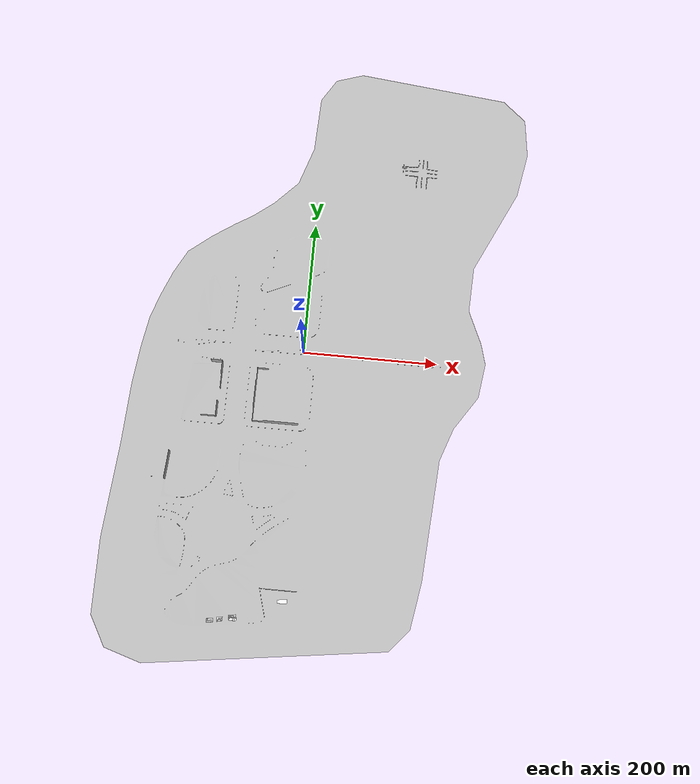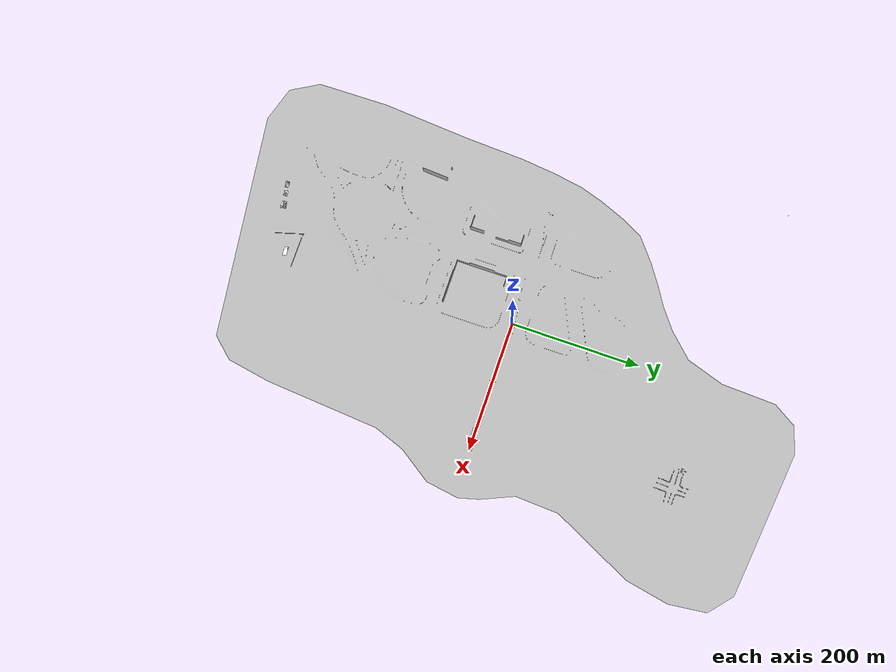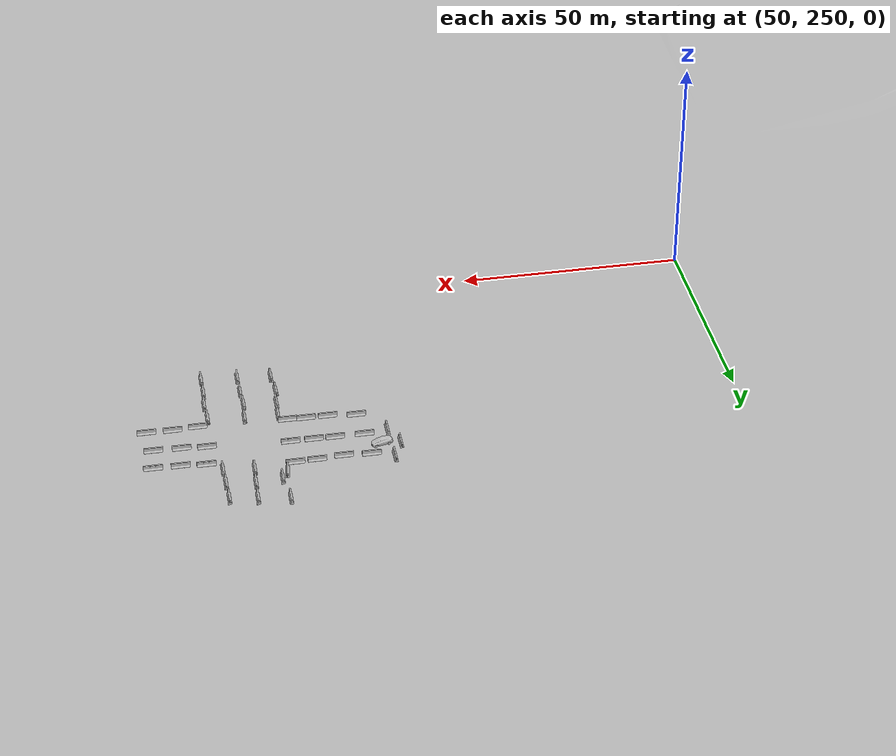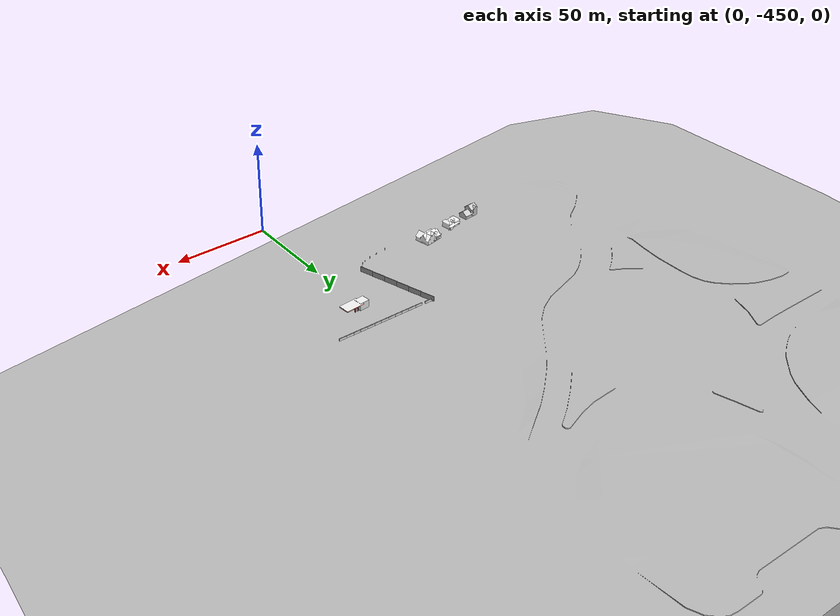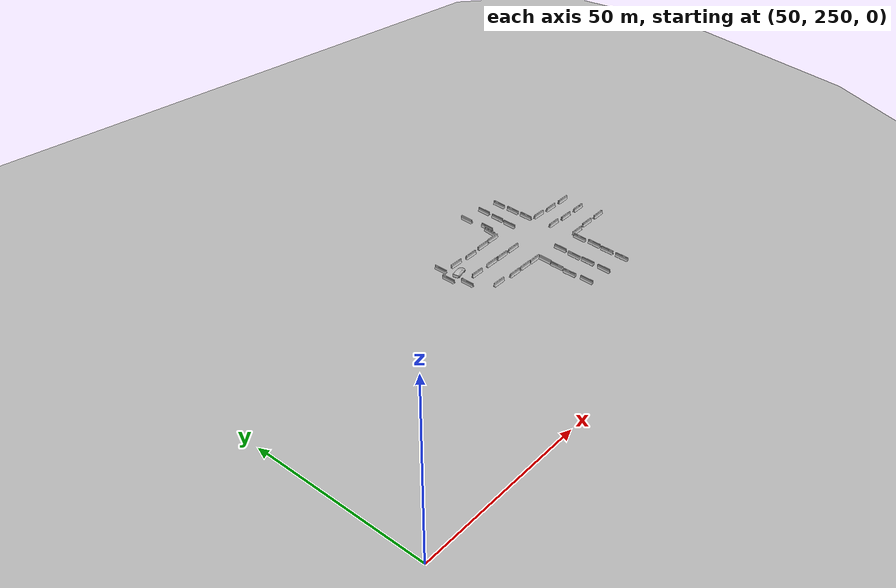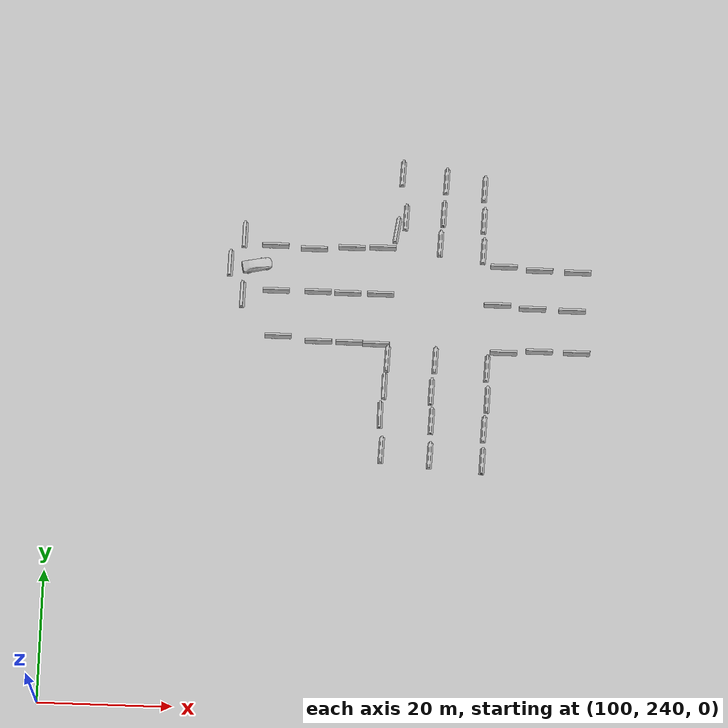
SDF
<sdf version="1.6">
 <world name="default">
  <light name="sun" type="directional">
   <pose>0 0 10 0 -0 0</pose>
   <diffuse>0.8 0.8 0.8 1</diffuse>
   <specular>0.2 0.2 0.2 1</specular>
   <attenuation>
    <range>1000</range>
    <constant>0.9</constant>
    <linear>0.01</linear>
    <quadratic>0.001</quadratic>
   </attenuation>
   <direction>-0.5 0.1 -0.9</direction>
  </light>
  <model name="cafe">
   <pose>-3.41959 -1.35212 0 0 -0 0</pose>
   <static>1</static>
   <link name="link">
    <collision name="collision">
     <geometry><mesh><scale>0.254 0.254 0.254</scale><uri>model://mcity/meshes/mcity.obj</uri></mesh></geometry>
    </collision>
    <visual name="visual">
     <geometry><mesh><scale>0.254 0.254 0.254</scale><uri>model://mcity/meshes/mcity.obj</uri></mesh></geometry>
    </visual>
   </link>
  </model>
  <gravity>0 0 -9.8</gravity>
  <magnetic_field>6e-06 2.3e-05 -4.2e-05</magnetic_field>
  <atmosphere type="adiabatic"/>
  <physics name="default_physics" default="0" type="ode">
   <max_step_size>0.001</max_step_size>
   <real_time_factor>1</real_time_factor>
   <real_time_update_rate>1000</real_time_update_rate>
  </physics>
  <scene><ambient>0.4 0.4 0.4 1</ambient><background>0.7 0.7 0.7 1</background><shadows>1</shadows></scene>
  <audio><device>default</device></audio>
  <spherical_coordinates>
   <surface_model>EARTH_WGS84</surface_model>
   <latitude_deg>0</latitude_deg>
   <longitude_deg>0</longitude_deg>
   <elevation>0</elevation>
   <heading_deg>0</heading_deg>
  </spherical_coordinates>
  <model name="Gas Station">
   <static>1</static>
   <link name="link">
    <collision name="collision">
     <geometry><mesh><uri>model://gas_station/meshes/gas_station.dae</uri></mesh></geometry>
    </collision>
    <visual name="visual">
     <geometry><mesh><uri>model://gas_station/meshes/gas_station.dae</uri></mesh></geometry>
     <material>
      <script>
       <uri>model://gas_station/materials/scripts</uri>
       <uri>model://gas_station/materials/textures</uri>
       <name>GasStation/Diffuse</name>
      </script>
      <shader type="normal_map_object_space"><normal_map>GasStation_Normal.png</normal_map></shader>
     </material>
    </visual>
   </link>
   <pose>3.60098 -363.272 0 0 -0 0.083826</pose>
  </model>
  <model name="jersey_barrier">
   <static>1</static>
   <link name="link">
    <visual name="visual">
     <geometry><mesh><uri>model://jersey_barrier/meshes/jersey_barrier.dae</uri></mesh></geometry>
    </visual>
    <collision name="upright">
     <pose>0 0 0.5715 0 -0 0</pose>
     <geometry><box><size>4.06542 0.3063 1.143</size></box></geometry>
    </collision>
    <collision name="base">
     <pose>0 0 0.032258 0 -0 0</pose>
     <geometry><box><size>4.06542 0.8107 0.064516</size></box></geometry>
    </collision>
    <collision name="base2">
     <pose>0 0 0.1 0 -0 0</pose>
     <geometry><box><size>4.06542 0.65 0.1</size></box></geometry>
    </collision>
    <collision name="base3">
     <pose>0 0 0.2 0 -0 0</pose>
     <geometry><box><size>4.06542 0.5 0.1</size></box></geometry>
    </collision>
    <collision name="left-angle">
     <pose>0 -0.224 0.2401 0.9 -0 0</pose>
     <geometry><box><size>4.06542 0.5 0.064516</size></box></geometry>
    </collision>
    <collision name="right-angle">
     <pose>0 0.224 0.2401 -0.9 0 0</pose>
     <geometry><box><size>4.06542 0.5 0.064516</size></box></geometry>
    </collision>
   </link>
   <pose>-27.7486 -347.795 0 0 -0 0</pose>
  </model>
  <model name="jersey_barrier_clone">
   <static>1</static>
   <link name="link">
    <visual name="visual">
     <geometry><mesh><uri>model://jersey_barrier/meshes/jersey_barrier.dae</uri></mesh></geometry>
    </visual>
    <collision name="upright">
     <pose>0 0 0.5715 0 -0 0</pose>
     <geometry><box><size>4.06542 0.3063 1.143</size></box></geometry>
    </collision>
    <collision name="base">
     <pose>0 0 0.032258 0 -0 0</pose>
     <geometry><box><size>4.06542 0.8107 0.064516</size></box></geometry>
    </collision>
    <collision name="base2">
     <pose>0 0 0.1 0 -0 0</pose>
     <geometry><box><size>4.06542 0.65 0.1</size></box></geometry>
    </collision>
    <collision name="base3">
     <pose>0 0 0.2 0 -0 0</pose>
     <geometry><box><size>4.06542 0.5 0.1</size></box></geometry>
    </collision>
    <collision name="left-angle">
     <pose>0 -0.224 0.2401 0.9 -0 0</pose>
     <geometry><box><size>4.06542 0.5 0.064516</size></box></geometry>
    </collision>
    <collision name="right-angle">
     <pose>0 0.224 0.2401 -0.9 0 0</pose>
     <geometry><box><size>4.06542 0.5 0.064516</size></box></geometry>
    </collision>
   </link>
   <pose>-22 -348 0 0 -0 0</pose>
  </model>
  <model name="jersey_barrier_clone_clone">
   <static>1</static>
   <link name="link">
    <visual name="visual">
     <geometry><mesh><uri>model://jersey_barrier/meshes/jersey_barrier.dae</uri></mesh></geometry>
    </visual>
    <collision name="upright">
     <pose>0 0 0.5715 0 -0 0</pose>
     <geometry><box><size>4.06542 0.3063 1.143</size></box></geometry>
    </collision>
    <collision name="base">
     <pose>0 0 0.032258 0 -0 0</pose>
     <geometry><box><size>4.06542 0.8107 0.064516</size></box></geometry>
    </collision>
    <collision name="base2">
     <pose>0 0 0.1 0 -0 0</pose>
     <geometry><box><size>4.06542 0.65 0.1</size></box></geometry>
    </collision>
    <collision name="base3">
     <pose>0 0 0.2 0 -0 0</pose>
     <geometry><box><size>4.06542 0.5 0.1</size></box></geometry>
    </collision>
    <collision name="left-angle">
     <pose>0 -0.224 0.2401 0.9 -0 0</pose>
     <geometry><box><size>4.06542 0.5 0.064516</size></box></geometry>
    </collision>
    <collision name="right-angle">
     <pose>0 0.224 0.2401 -0.9 0 0</pose>
     <geometry><box><size>4.06542 0.5 0.064516</size></box></geometry>
    </collision>
   </link>
   <pose>-18 -348 0 0 -0 0</pose>
  </model>
  <model name="jersey_barrier_clone_clone_clone">
   <static>1</static>
   <link name="link">
    <visual name="visual">
     <geometry><mesh><uri>model://jersey_barrier/meshes/jersey_barrier.dae</uri></mesh></geometry>
    </visual>
    <collision name="upright">
     <pose>0 0 0.5715 0 -0 0</pose>
     <geometry><box><size>4.06542 0.3063 1.143</size></box></geometry>
    </collision>
    <collision name="base">
     <pose>0 0 0.032258 0 -0 0</pose>
     <geometry><box><size>4.06542 0.8107 0.064516</size></box></geometry>
    </collision>
    <collision name="base2">
     <pose>0 0 0.1 0 -0 0</pose>
     <geometry><box><size>4.06542 0.65 0.1</size></box></geometry>
    </collision>
    <collision name="base3">
     <pose>0 0 0.2 0 -0 0</pose>
     <geometry><box><size>4.06542 0.5 0.1</size></box></geometry>
    </collision>
    <collision name="left-angle">
     <pose>0 -0.224 0.2401 0.9 -0 0</pose>
     <geometry><box><size>4.06542 0.5 0.064516</size></box></geometry>
    </collision>
    <collision name="right-angle">
     <pose>0 0.224 0.2401 -0.9 0 0</pose>
     <geometry><box><size>4.06542 0.5 0.064516</size></box></geometry>
    </collision>
   </link>
   <pose>-14.0215 -348.019 0 0 -0 0</pose>
  </model>
  <model name="jersey_barrier_clone_clone_clone_clone">
   <static>1</static>
   <link name="link">
    <visual name="visual">
     <geometry><mesh><uri>model://jersey_barrier/meshes/jersey_barrier.dae</uri></mesh></geometry>
    </visual>
    <collision name="upright">
     <pose>0 0 0.5715 0 -0 0</pose>
     <geometry><box><size>4.06542 0.3063 1.143</size></box></geometry>
    </collision>
    <collision name="base">
     <pose>0 0 0.032258 0 -0 0</pose>
     <geometry><box><size>4.06542 0.8107 0.064516</size></box></geometry>
    </collision>
    <collision name="base2">
     <pose>0 0 0.1 0 -0 0</pose>
     <geometry><box><size>4.06542 0.65 0.1</size></box></geometry>
    </collision>
    <collision name="base3">
     <pose>0 0 0.2 0 -0 0</pose>
     <geometry><box><size>4.06542 0.5 0.1</size></box></geometry>
    </collision>
    <collision name="left-angle">
     <pose>0 -0.224 0.2401 0.9 -0 0</pose>
     <geometry><box><size>4.06542 0.5 0.064516</size></box></geometry>
    </collision>
    <collision name="right-angle">
     <pose>0 0.224 0.2401 -0.9 0 0</pose>
     <geometry><box><size>4.06542 0.5 0.064516</size></box></geometry>
    </collision>
   </link>
   <pose>-10 -348 0 0 -0 0</pose>
  </model>
  <model name="jersey_barrier_clone_clone_clone_clone_clone">
   <static>1</static>
   <link name="link">
    <visual name="visual">
     <geometry><mesh><uri>model://jersey_barrier/meshes/jersey_barrier.dae</uri></mesh></geometry>
    </visual>
    <collision name="upright">
     <pose>0 0 0.5715 0 -0 0</pose>
     <geometry><box><size>4.06542 0.3063 1.143</size></box></geometry>
    </collision>
    <collision name="base">
     <pose>0 0 0.032258 0 -0 0</pose>
     <geometry><box><size>4.06542 0.8107 0.064516</size></box></geometry>
    </collision>
    <collision name="base2">
     <pose>0 0 0.1 0 -0 0</pose>
     <geometry><box><size>4.06542 0.65 0.1</size></box></geometry>
    </collision>
    <collision name="base3">
     <pose>0 0 0.2 0 -0 0</pose>
     <geometry><box><size>4.06542 0.5 0.1</size></box></geometry>
    </collision>
    <collision name="left-angle">
     <pose>0 -0.224 0.2401 0.9 -0 0</pose>
     <geometry><box><size>4.06542 0.5 0.064516</size></box></geometry>
    </collision>
    <collision name="right-angle">
     <pose>0 0.224 0.2401 -0.9 0 0</pose>
     <geometry><box><size>4.06542 0.5 0.064516</size></box></geometry>
    </collision>
   </link>
   <pose>-6 -348 0 0 -0 0</pose>
  </model>
  <model name="jersey_barrier_clone_clone_clone_clone_clone_clone">
   <static>1</static>
   <link name="link">
    <visual name="visual">
     <geometry><mesh><uri>model://jersey_barrier/meshes/jersey_barrier.dae</uri></mesh></geometry>
    </visual>
    <collision name="upright">
     <pose>0 0 0.5715 0 -0 0</pose>
     <geometry><box><size>4.06542 0.3063 1.143</size></box></geometry>
    </collision>
    <collision name="base">
     <pose>0 0 0.032258 0 -0 0</pose>
     <geometry><box><size>4.06542 0.8107 0.064516</size></box></geometry>
    </collision>
    <collision name="base2">
     <pose>0 0 0.1 0 -0 0</pose>
     <geometry><box><size>4.06542 0.65 0.1</size></box></geometry>
    </collision>
    <collision name="base3">
     <pose>0 0 0.2 0 -0 0</pose>
     <geometry><box><size>4.06542 0.5 0.1</size></box></geometry>
    </collision>
    <collision name="left-angle">
     <pose>0 -0.224 0.2401 0.9 -0 0</pose>
     <geometry><box><size>4.06542 0.5 0.064516</size></box></geometry>
    </collision>
    <collision name="right-angle">
     <pose>0 0.224 0.2401 -0.9 0 0</pose>
     <geometry><box><size>4.06542 0.5 0.064516</size></box></geometry>
    </collision>
   </link>
   <pose>-2 -348 0 0 -0 0</pose>
  </model>
  <model name="jersey_barrier_clone_clone_clone_clone_clone_clone_clone">
   <static>1</static>
   <link name="link">
    <visual name="visual">
     <geometry><mesh><uri>model://jersey_barrier/meshes/jersey_barrier.dae</uri></mesh></geometry>
    </visual>
    <collision name="upright">
     <pose>0 0 0.5715 0 -0 0</pose>
     <geometry><box><size>4.06542 0.3063 1.143</size></box></geometry>
    </collision>
    <collision name="base">
     <pose>0 0 0.032258 0 -0 0</pose>
     <geometry><box><size>4.06542 0.8107 0.064516</size></box></geometry>
    </collision>
    <collision name="base2">
     <pose>0 0 0.1 0 -0 0</pose>
     <geometry><box><size>4.06542 0.65 0.1</size></box></geometry>
    </collision>
    <collision name="base3">
     <pose>0 0 0.2 0 -0 0</pose>
     <geometry><box><size>4.06542 0.5 0.1</size></box></geometry>
    </collision>
    <collision name="left-angle">
     <pose>0 -0.224 0.2401 0.9 -0 0</pose>
     <geometry><box><size>4.06542 0.5 0.064516</size></box></geometry>
    </collision>
    <collision name="right-angle">
     <pose>0 0.224 0.2401 -0.9 0 0</pose>
     <geometry><box><size>4.06542 0.5 0.064516</size></box></geometry>
    </collision>
   </link>
   <pose>6 -348 0 0 -0 0</pose>
  </model>
  <model name="jersey_barrier_clone_clone_clone_clone_clone_clone_clone_clone">
   <static>1</static>
   <link name="link">
    <visual name="visual">
     <geometry><mesh><uri>model://jersey_barrier/meshes/jersey_barrier.dae</uri></mesh></geometry>
    </visual>
    <collision name="upright">
     <pose>0 0 0.5715 0 -0 0</pose>
     <geometry><box><size>4.06542 0.3063 1.143</size></box></geometry>
    </collision>
    <collision name="base">
     <pose>0 0 0.032258 0 -0 0</pose>
     <geometry><box><size>4.06542 0.8107 0.064516</size></box></geometry>
    </collision>
    <collision name="base2">
     <pose>0 0 0.1 0 -0 0</pose>
     <geometry><box><size>4.06542 0.65 0.1</size></box></geometry>
    </collision>
    <collision name="base3">
     <pose>0 0 0.2 0 -0 0</pose>
     <geometry><box><size>4.06542 0.5 0.1</size></box></geometry>
    </collision>
    <collision name="left-angle">
     <pose>0 -0.224 0.2401 0.9 -0 0</pose>
     <geometry><box><size>4.06542 0.5 0.064516</size></box></geometry>
    </collision>
    <collision name="right-angle">
     <pose>0 0.224 0.2401 -0.9 0 0</pose>
     <geometry><box><size>4.06542 0.5 0.064516</size></box></geometry>
    </collision>
   </link>
   <pose>2 -348 0 0 -0 0</pose>
  </model>
  <model name="jersey_barrier_clone_clone_clone_clone_clone_clone_clone_clone_0">
   <static>1</static>
   <link name="link">
    <visual name="visual">
     <geometry><mesh><uri>model://jersey_barrier/meshes/jersey_barrier.dae</uri></mesh></geometry>
    </visual>
    <collision name="upright">
     <pose>0 0 0.5715 0 -0 0</pose>
     <geometry><box><size>4.06542 0.3063 1.143</size></box></geometry>
    </collision>
    <collision name="base">
     <pose>0 0 0.032258 0 -0 0</pose>
     <geometry><box><size>4.06542 0.8107 0.064516</size></box></geometry>
    </collision>
    <collision name="base2">
     <pose>0 0 0.1 0 -0 0</pose>
     <geometry><box><size>4.06542 0.65 0.1</size></box></geometry>
    </collision>
    <collision name="base3">
     <pose>0 0 0.2 0 -0 0</pose>
     <geometry><box><size>4.06542 0.5 0.1</size></box></geometry>
    </collision>
    <collision name="left-angle">
     <pose>0 -0.224 0.2401 0.9 -0 0</pose>
     <geometry><box><size>4.06542 0.5 0.064516</size></box></geometry>
    </collision>
    <collision name="right-angle">
     <pose>0 0.224 0.2401 -0.9 0 0</pose>
     <geometry><box><size>4.06542 0.5 0.064516</size></box></geometry>
    </collision>
   </link>
   <pose>10 -348 0 0 -0 0</pose>
  </model>
  <model name="jersey_barrier_clone_clone_clone_clone_clone_clone_clone_clone_0_clone">
   <static>1</static>
   <link name="link">
    <visual name="visual">
     <geometry><mesh><uri>model://jersey_barrier/meshes/jersey_barrier.dae</uri></mesh></geometry>
    </visual>
    <collision name="upright">
     <pose>0 0 0.5715 0 -0 0</pose>
     <geometry><box><size>4.06542 0.3063 1.143</size></box></geometry>
    </collision>
    <collision name="base">
     <pose>0 0 0.032258 0 -0 0</pose>
     <geometry><box><size>4.06542 0.8107 0.064516</size></box></geometry>
    </collision>
    <collision name="base2">
     <pose>0 0 0.1 0 -0 0</pose>
     <geometry><box><size>4.06542 0.65 0.1</size></box></geometry>
    </collision>
    <collision name="base3">
     <pose>0 0 0.2 0 -0 0</pose>
     <geometry><box><size>4.06542 0.5 0.1</size></box></geometry>
    </collision>
    <collision name="left-angle">
     <pose>0 -0.224 0.2401 0.9 -0 0</pose>
     <geometry><box><size>4.06542 0.5 0.064516</size></box></geometry>
    </collision>
    <collision name="right-angle">
     <pose>0 0.224 0.2401 -0.9 0 0</pose>
     <geometry><box><size>4.06542 0.5 0.064516</size></box></geometry>
    </collision>
   </link>
   <pose>14 -348 0 0 -0 0</pose>
  </model>
  <model name="jersey_barrier_clone_clone_clone_clone_clone_clone_clone_clone_0_clone_clone">
   <static>1</static>
   <link name="link">
    <visual name="visual">
     <geometry><mesh><uri>model://jersey_barrier/meshes/jersey_barrier.dae</uri></mesh></geometry>
    </visual>
    <collision name="upright">
     <pose>0 0 0.5715 0 -0 0</pose>
     <geometry><box><size>4.06542 0.3063 1.143</size></box></geometry>
    </collision>
    <collision name="base">
     <pose>0 0 0.032258 0 -0 0</pose>
     <geometry><box><size>4.06542 0.8107 0.064516</size></box></geometry>
    </collision>
    <collision name="base2">
     <pose>0 0 0.1 0 -0 0</pose>
     <geometry><box><size>4.06542 0.65 0.1</size></box></geometry>
    </collision>
    <collision name="base3">
     <pose>0 0 0.2 0 -0 0</pose>
     <geometry><box><size>4.06542 0.5 0.1</size></box></geometry>
    </collision>
    <collision name="left-angle">
     <pose>0 -0.224 0.2401 0.9 -0 0</pose>
     <geometry><box><size>4.06542 0.5 0.064516</size></box></geometry>
    </collision>
    <collision name="right-angle">
     <pose>0 0.224 0.2401 -0.9 0 0</pose>
     <geometry><box><size>4.06542 0.5 0.064516</size></box></geometry>
    </collision>
   </link>
   <pose>18 -348 0 0 -0 0</pose>
  </model>
  <model name="jersey_barrier_clone_clone_clone_clone_clone_clone_clone_clone_0_clone_clone_clone">
   <static>1</static>
   <link name="link">
    <visual name="visual">
     <geometry><mesh><uri>model://jersey_barrier/meshes/jersey_barrier.dae</uri></mesh></geometry>
    </visual>
    <collision name="upright">
     <pose>0 0 0.5715 0 -0 0</pose>
     <geometry><box><size>4.06542 0.3063 1.143</size></box></geometry>
    </collision>
    <collision name="base">
     <pose>0 0 0.032258 0 -0 0</pose>
     <geometry><box><size>4.06542 0.8107 0.064516</size></box></geometry>
    </collision>
    <collision name="base2">
     <pose>0 0 0.1 0 -0 0</pose>
     <geometry><box><size>4.06542 0.65 0.1</size></box></geometry>
    </collision>
    <collision name="base3">
     <pose>0 0 0.2 0 -0 0</pose>
     <geometry><box><size>4.06542 0.5 0.1</size></box></geometry>
    </collision>
    <collision name="left-angle">
     <pose>0 -0.224 0.2401 0.9 -0 0</pose>
     <geometry><box><size>4.06542 0.5 0.064516</size></box></geometry>
    </collision>
    <collision name="right-angle">
     <pose>0 0.224 0.2401 -0.9 0 0</pose>
     <geometry><box><size>4.06542 0.5 0.064516</size></box></geometry>
    </collision>
   </link>
   <pose>22 -348 0 0 -0 0</pose>
  </model>
  <model name="grey_wall">
   <static>1</static>
   <link name="link">
    <pose>0 0 1.4 0 -0 0</pose>
    <collision name="collision"><geometry><box><size>7.5 0.2 2.8</size></box></geometry></collision>
    <visual name="visual">
     <cast_shadows>0</cast_shadows>
     <geometry><box><size>7.5 0.2 2.8</size></box></geometry>
     <material>
      <script>
       <uri>model://grey_wall/materials/scripts</uri>
       <uri>model://grey_wall/materials/textures</uri>
       <name>vrc/grey_wall</name>
      </script>
     </material>
    </visual>
   </link>
   <pose>-29 -350 0 0 -0 1.87601</pose>
  </model>
  <model name="grey_wall_clone">
   <static>1</static>
   <link name="link">
    <pose>0 0 1.4 0 -0 0</pose>
    <collision name="collision"><geometry><box><size>7.5 0.2 2.8</size></box></geometry></collision>
    <visual name="visual">
     <cast_shadows>0</cast_shadows>
     <geometry><box><size>7.5 0.2 2.8</size></box></geometry>
     <material>
      <script>
       <uri>model://grey_wall/materials/scripts</uri>
       <uri>model://grey_wall/materials/textures</uri>
       <name>vrc/grey_wall</name>
      </script>
     </material>
    </visual>
   </link>
   <pose>-27 -357 0 0 -0 1.87601</pose>
  </model>
  <model name="grey_wall_clone_0">
   <static>1</static>
   <link name="link">
    <pose>0 0 1.4 0 -0 0</pose>
    <collision name="collision"><geometry><box><size>7.5 0.2 2.8</size></box></geometry></collision>
    <visual name="visual">
     <cast_shadows>0</cast_shadows>
     <geometry><box><size>7.5 0.2 2.8</size></box></geometry>
     <material>
      <script>
       <uri>model://grey_wall/materials/scripts</uri>
       <uri>model://grey_wall/materials/textures</uri>
       <name>vrc/grey_wall</name>
      </script>
     </material>
    </visual>
   </link>
   <pose>-25 -364 0 0 -0 1.87601</pose>
  </model>
  <model name="grey_wall_clone_0_clone">
   <static>1</static>
   <link name="link">
    <pose>0 0 1.4 0 -0 0</pose>
    <collision name="collision"><geometry><box><size>7.5 0.2 2.8</size></box></geometry></collision>
    <visual name="visual">
     <cast_shadows>0</cast_shadows>
     <geometry><box><size>7.5 0.2 2.8</size></box></geometry>
     <material>
      <script>
       <uri>model://grey_wall/materials/scripts</uri>
       <uri>model://grey_wall/materials/textures</uri>
       <name>vrc/grey_wall</name>
      </script>
     </material>
    </visual>
   </link>
   <pose>-23 -371 0 0 -0 1.87601</pose>
  </model>
  <model name="grey_wall_clone_0_clone_clone">
   <static>1</static>
   <link name="link">
    <pose>0 0 1.4 0 -0 0</pose>
    <collision name="collision"><geometry><box><size>7.5 0.2 2.8</size></box></geometry></collision>
    <visual name="visual">
     <cast_shadows>0</cast_shadows>
     <geometry><box><size>7.5 0.2 2.8</size></box></geometry>
     <material>
      <script>
       <uri>model://grey_wall/materials/scripts</uri>
       <uri>model://grey_wall/materials/textures</uri>
       <name>vrc/grey_wall</name>
      </script>
     </material>
    </visual>
   </link>
   <pose>-21 -378 0 0 -0 1.87601</pose>
  </model>
  <model name="grey_wall_clone_0_clone_clone_clone">
   <static>1</static>
   <link name="link">
    <pose>0 0 1.4 0 -0 0</pose>
    <collision name="collision"><geometry><box><size>7.5 0.2 2.8</size></box></geometry></collision>
    <visual name="visual">
     <cast_shadows>0</cast_shadows>
     <geometry><box><size>7.5 0.2 2.8</size></box></geometry>
     <material>
      <script>
       <uri>model://grey_wall/materials/scripts</uri>
       <uri>model://grey_wall/materials/textures</uri>
       <name>vrc/grey_wall</name>
      </script>
     </material>
    </visual>
   </link>
   <pose>-19 -385 0 0 -0 1.87601</pose>
  </model>
  <model name="House 1">
   <static>1</static>
   <link name="link">
    <collision name="collision">
     <geometry><mesh><uri>model://house_1/meshes/house_1.dae</uri></mesh></geometry>
    </collision>
    <visual name="visual">
     <geometry><mesh><uri>model://house_1/meshes/house_1.dae</uri></mesh></geometry>
     <material>
      <script>
       <uri>model://house_1/materials/scripts</uri>
       <uri>model://house_1/materials/textures</uri>
       <name>House_1/Diffuse</name>
      </script>
      <shader type="normal_map_object_space"><normal_map>House_1_Normal.png</normal_map></shader>
     </material>
    </visual>
   </link>
   <pose>-63.4144 -391.538 0 0 -0 0.178783</pose>
  </model>
  <model name="House 2">
   <static>1</static>
   <link name="link">
    <collision name="collision">
     <geometry><mesh><uri>model://house_2/meshes/house_2.dae</uri></mesh></geometry>
    </collision>
    <visual name="visual">
     <geometry><mesh><uri>model://house_2/meshes/house_2.dae</uri></mesh></geometry>
     <material>
      <script>
       <uri>model://house_2/materials/scripts</uri>
       <uri>model://house_2/materials/textures</uri>
       <uri>model://house_1/materials/textures</uri>
       <name>House_2/Diffuse</name>
      </script>
      <shader type="normal_map_object_space">
       <normal_map>model://house_1/materials/textures/House_1_Normal.png</normal_map>
      </shader>
     </material>
    </visual>
   </link>
   <pose>-82.0852 -395.523 0 0 -0 0.112755</pose>
  </model>
  <model name="House 3">
   <static>1</static>
   <link name="link">
    <collision name="collision">
     <geometry><mesh><uri>model://house_3/meshes/house_3.dae</uri></mesh></geometry>
    </collision>
    <visual name="visual">
     <geometry><mesh><uri>model://house_3/meshes/house_3.dae</uri></mesh></geometry>
     <material>
      <script>
       <uri>model://house_3/materials/scripts</uri>
       <uri>model://house_3/materials/textures</uri>
       <uri>model://house_1/materials/textures</uri>
       <name>House_3/Diffuse</name>
      </script>
      <shader type="normal_map_object_space">
       <normal_map>model://house_1/materials/textures/House_1_Normal.png</normal_map>
      </shader>
     </material>
    </visual>
   </link>
   <pose>-94.9389 -397.723 0 0 -0 0.112475</pose>
  </model>
  <model name="Construction Cone">
   <link name="link">
    <collision name="collision">
     <geometry>
      <mesh><scale>10 10 10</scale><uri>model://construction_cone/meshes/construction_cone.dae</uri></mesh>
     </geometry>
    </collision>
    <visual name="visual">
     <geometry>
      <mesh><scale>10 10 10</scale><uri>model://construction_cone/meshes/construction_cone.dae</uri></mesh>
     </geometry>
    </visual>
    <inertial>
     <inertia><ixx>1</ixx><ixy>0</ixy><ixz>0</ixz><iyy>1</iyy><iyz>0</iyz><izz>1</izz></inertia>
     <mass>1</mass>
    </inertial>
   </link>
   <pose>-19 -389.557 0 0 -0 0</pose>
  </model>
  <model name="Construction Cone_clone">
   <link name="link">
    <collision name="collision">
     <geometry>
      <mesh><scale>10 10 10</scale><uri>model://construction_cone/meshes/construction_cone.dae</uri></mesh>
     </geometry>
    </collision>
    <visual name="visual">
     <geometry>
      <mesh><scale>10 10 10</scale><uri>model://construction_cone/meshes/construction_cone.dae</uri></mesh>
     </geometry>
    </visual>
    <inertial>
     <inertia><ixx>1</ixx><ixy>0</ixy><ixz>0</ixz><iyy>1</iyy><iyz>0</iyz><izz>1</izz></inertia>
     <mass>1</mass>
    </inertial>
   </link>
   <pose>-20.5705 -391.331 0 0 -0 0</pose>
  </model>
  <model name="Construction Cone_clone_clone">
   <link name="link">
    <collision name="collision">
     <geometry>
      <mesh><scale>10 10 10</scale><uri>model://construction_cone/meshes/construction_cone.dae</uri></mesh>
     </geometry>
    </collision>
    <visual name="visual">
     <geometry>
      <mesh><scale>10 10 10</scale><uri>model://construction_cone/meshes/construction_cone.dae</uri></mesh>
     </geometry>
    </visual>
    <inertial>
     <inertia><ixx>1</ixx><ixy>0</ixy><ixz>0</ixz><iyy>1</iyy><iyz>0</iyz><izz>1</izz></inertia>
     <mass>1</mass>
    </inertial>
   </link>
   <pose>-22.3249 -393.096 0 0 -0 0</pose>
  </model>
  <model name="Construction Cone_clone_clone_clone">
   <link name="link">
    <collision name="collision">
     <geometry>
      <mesh><scale>10 10 10</scale><uri>model://construction_cone/meshes/construction_cone.dae</uri></mesh>
     </geometry>
    </collision>
    <visual name="visual">
     <geometry>
      <mesh><scale>10 10 10</scale><uri>model://construction_cone/meshes/construction_cone.dae</uri></mesh>
     </geometry>
    </visual>
    <inertial>
     <inertia><ixx>1</ixx><ixy>0</ixy><ixz>0</ixz><iyy>1</iyy><iyz>0</iyz><izz>1</izz></inertia>
     <mass>1</mass>
    </inertial>
   </link>
   <pose>-25.1263 -394.655 -9e-06 0 1e-06 0</pose>
  </model>
  <model name="Construction Cone_clone_clone_clone_clone">
   <link name="link">
    <collision name="collision">
     <geometry>
      <mesh><scale>10 10 10</scale><uri>model://construction_cone/meshes/construction_cone.dae</uri></mesh>
     </geometry>
    </collision>
    <visual name="visual">
     <geometry>
      <mesh><scale>10 10 10</scale><uri>model://construction_cone/meshes/construction_cone.dae</uri></mesh>
     </geometry>
    </visual>
    <inertial>
     <inertia><ixx>1</ixx><ixy>0</ixy><ixz>0</ixz><iyy>1</iyy><iyz>0</iyz><izz>1</izz></inertia>
     <mass>1</mass>
    </inertial>
   </link>
   <pose>-28.6583 -395.535 -9e-06 -1e-06 0 0</pose>
  </model>
  <model name="Construction Cone_clone_clone_clone_clone_clone">
   <link name="link">
    <collision name="collision">
     <geometry>
      <mesh><scale>10 10 10</scale><uri>model://construction_cone/meshes/construction_cone.dae</uri></mesh>
     </geometry>
    </collision>
    <visual name="visual">
     <geometry>
      <mesh><scale>10 10 10</scale><uri>model://construction_cone/meshes/construction_cone.dae</uri></mesh>
     </geometry>
    </visual>
    <inertial>
     <inertia><ixx>1</ixx><ixy>0</ixy><ixz>0</ixz><iyy>1</iyy><iyz>0</iyz><izz>1</izz></inertia>
     <mass>1</mass>
    </inertial>
   </link>
   <pose>-33.3133 -396.401 0 0 -0 0</pose>
  </model>
  <model name="Construction Cone_clone_clone_clone_clone_clone_clone">
   <link name="link">
    <collision name="collision">
     <geometry>
      <mesh><scale>10 10 10</scale><uri>model://construction_cone/meshes/construction_cone.dae</uri></mesh>
     </geometry>
    </collision>
    <visual name="visual">
     <geometry>
      <mesh><scale>10 10 10</scale><uri>model://construction_cone/meshes/construction_cone.dae</uri></mesh>
     </geometry>
    </visual>
    <inertial>
     <inertia><ixx>1</ixx><ixy>0</ixy><ixz>0</ixz><iyy>1</iyy><iyz>0</iyz><izz>1</izz></inertia>
     <mass>1</mass>
    </inertial>
   </link>
   <pose>-39.2634 -397.191 -1e-05 0 -0 0</pose>
  </model>
  <model name="cloverleaf_interchange">
   <static>1</static>
   <link name="link">
    <collision name="collision">
     <geometry>
      <mesh>
       <uri>model://cloverleaf_interchange/meshes/cloverleaf.obj</uri>
       <scale>0.0254 0.0254 0.0254</scale>
      </mesh>
     </geometry>
    </collision>
    <visual name="visual">
     <geometry>
      <mesh>
       <uri>model://cloverleaf_interchange/meshes/cloverleaf.obj</uri>
       <scale>0.0254 0.0254 0.0254</scale>
      </mesh>
     </geometry>
    </visual>
   </link>
   <pose>-295.324 348.572 0 0 -0 0</pose>
  </model>
  <model name="Speed limit">
   <static>1</static>
   <link name="link">
    <collision name="collision">
     <geometry>
      <mesh><scale>10 10 10</scale><uri>model://speed_limit_sign/meshes/speed_limit_sign.dae</uri></mesh>
     </geometry>
    </collision>
    <visual name="visual">
     <geometry>
      <mesh><scale>10 10 10</scale><uri>model://speed_limit_sign/meshes/speed_limit_sign.dae</uri></mesh>
     </geometry>
    </visual>
   </link>
   <pose>93.9624 -21.3385 0 0 -0 0</pose>
  </model>
  <model name="prius">
   <link name="base_link">
    <inertial>
     <mass>1</mass>
     <inertia><ixx>0.001</ixx><ixy>0</ixy><ixz>0</ixz><iyy>0.001</iyy><iyz>0</iyz><izz>0.001</izz></inertia>
    </inertial>
   </link>
   <link name="chassis">
    <pose>1.45 0 0 0 -0 1.57</pose>
    <inertial>
     <pose>-0 -0.00441 0.483098 0 -0 1.5708</pose>
     <mass>1372</mass>
     <inertia>
      <ixx>2591.33</ixx>
      <ixy>0.000203846</ixy>
      <ixz>-1.05374</ixz>
      <iyy>657</iyy>
      <iyz>3.87061e-06</iyz>
      <izz>2749.84</izz>
     </inertia>
    </inertial>
    <collision name="chassis_collision">
     <pose>0 0.05 0.625 0 -0 0</pose>
     <geometry><box><size>1.7526 2.1 0.95</size></box></geometry>
    </collision>
    <collision name="chassis_fixed_joint_lump__front_bumper_collision_1">
     <pose>0 -2 0.458488 0 -0 0</pose>
     <geometry><box><size>1.33728 0.48 0.566691</size></box></geometry>
    </collision>
    <collision name="chassis_fixed_joint_lump__hood_collision_2">
     <pose>0 -1.90084 0.676305 0.341247 -0 0</pose>
     <geometry><box><size>1.59797 0.493107 0.265468</size></box></geometry>
    </collision>
    <collision name="chassis_fixed_joint_lump__windshield_collision_3">
     <pose>0 -0.875105 1.03227 0.335476 -0 0</pose>
     <geometry><box><size>1.16838 1.65425 0.272347</size></box></geometry>
    </collision>
    <collision name="chassis_fixed_joint_lump__top_front_collision_4">
     <pose>0 0.161236 1.38604 0.13503 -0 0</pose>
     <geometry><box><size>1.27915 0.625988 0.171868</size></box></geometry>
    </collision>
    <collision name="chassis_fixed_joint_lump__top_rear_collision_5">
     <pose>0 0.817696 1.36007 -0.068997 0 0</pose>
     <geometry><box><size>1.28513 0.771189 0.226557</size></box></geometry>
    </collision>
    <collision name="chassis_fixed_joint_lump__rear_window_collision_6">
     <pose>0 1.64053 1.17513 -0.262017 0 0</pose>
     <geometry><box><size>1.26785 1.11634 0.244286</size></box></geometry>
    </collision>
    <collision name="chassis_fixed_joint_lump__trunk_collision_7">
     <pose>0 1.63706 0.88818 0 -0 0</pose>
     <geometry><box><size>1.78806 1.13899 0.482746</size></box></geometry>
    </collision>
    <collision name="chassis_fixed_joint_lump__back_bumper_collision_8">
     <pose>0 2.05445 0.57787 0 -0 0</pose>
     <geometry><box><size>1.78165 0.512093 0.581427</size></box></geometry>
    </collision>
    <visual name="chassis_visual">
     <geometry>
      <mesh>
       <scale>0.01 0.01 0.01</scale>
       <uri>/home/tejus/catkin_ws/src/Path-Tracking-Simulation/car_demo/prius_description/meshes/hybrid_body.obj</uri>
      </mesh>
     </geometry>
    </visual>
    <sensor name="back_camera_sensor" type="camera">
     <update_rate>30</update_rate>
     <camera name="back_camera">
      <horizontal_fov>1.39626</horizontal_fov>
      <image><width>800</width><height>800</height><format>R8G8B8</format></image>
      <clip><near>0.02</near><far>300</far></clip>
      <noise><type>gaussian</type><mean>0</mean><stddev>0.007</stddev></noise>
     </camera>
     <plugin name="back_camera_controller" filename="libgazebo_ros_camera.so">
      <alwaysOn>false</alwaysOn>
      <updateRate>0.0</updateRate>
      <cameraName>/prius/back_camera</cameraName>
      <imageTopicName>image_raw</imageTopicName>
      <cameraInfoTopicName>/prius/back_camera_info</cameraInfoTopicName>
      <frameName>camera_link</frameName>
      <hackBaseline>0.07</hackBaseline>
      <distortionK1>0.0</distortionK1>
      <distortionK2>0.0</distortionK2>
      <distortionK3>0.0</distortionK3>
      <distortionT1>0.0</distortionT1>
      <distortionT2>0.0</distortionT2>
      <robotNamespace>/</robotNamespace>
     </plugin>
     <pose>0 1.45 1.4 0 0.05 1.5707</pose>
    </sensor>
    <sensor name="back_left_far_sonar_sensor" type="ray">
     <ray>
      <scan>
       <horizontal>
        <samples>1</samples>
        <resolution>1</resolution>
        <min_angle>0</min_angle>
        <max_angle>0</max_angle>
       </horizontal>
       <vertical><samples>1</samples><min_angle>0</min_angle><max_angle>0</max_angle></vertical>
      </scan>
      <range><min>0.2</min><max>5</max><resolution>0.1</resolution></range>
     </ray>
     <plugin name="back_left_far_sonar_sensor" filename="libgazebo_ros_range.so">
      <topicName>/prius/back_sonar/left_far_range</topicName>
      <frameName>back_left_far_sonar_link</frameName>
      <robotNamespace>/</robotNamespace>
     </plugin>
     <always_on>0</always_on>
     <update_rate>5</update_rate>
     <visualize>0</visualize>
     <pose>0.7 2.4 0.5 0 -0 1.5707</pose>
    </sensor>
    <sensor name="back_left_middle_sonar_sensor" type="ray">
     <ray>
      <scan>
       <horizontal>
        <samples>1</samples>
        <resolution>1</resolution>
        <min_angle>0</min_angle>
        <max_angle>0</max_angle>
       </horizontal>
       <vertical><samples>1</samples><min_angle>0</min_angle><max_angle>0</max_angle></vertical>
      </scan>
      <range><min>0.2</min><max>5</max><resolution>0.1</resolution></range>
     </ray>
     <plugin name="back_left_middle_sonar_sensor" filename="libgazebo_ros_range.so">
      <topicName>/prius/back_sonar/left_middle_range</topicName>
      <frameName>back_left_middle_sonar_link</frameName>
      <robotNamespace>/</robotNamespace>
     </plugin>
     <always_on>0</always_on>
     <update_rate>5</update_rate>
     <visualize>0</visualize>
     <pose>0.24 2.4 0.5 0 -0 1.5707</pose>
    </sensor>
    <sensor name="back_right_far_sonar_sensor" type="ray">
     <ray>
      <scan>
       <horizontal>
        <samples>1</samples>
        <resolution>1</resolution>
        <min_angle>0</min_angle>
        <max_angle>0</max_angle>
       </horizontal>
       <vertical><samples>1</samples><min_angle>0</min_angle><max_angle>0</max_angle></vertical>
      </scan>
      <range><min>0.2</min><max>5</max><resolution>0.1</resolution></range>
     </ray>
     <plugin name="back_right_far_sonar_sensor" filename="libgazebo_ros_range.so">
      <topicName>/prius/back_sonar/right_far_range</topicName>
      <frameName>back_right_far_sonar_link</frameName>
      <robotNamespace>/</robotNamespace>
     </plugin>
     <always_on>0</always_on>
     <update_rate>5</update_rate>
     <visualize>0</visualize>
     <pose>-0.7 2.4 0.5 0 -0 1.5707</pose>
    </sensor>
    <sensor name="back_right_middle_sonar_sensor" type="ray">
     <ray>
      <scan>
       <horizontal>
        <samples>1</samples>
        <resolution>1</resolution>
        <min_angle>0</min_angle>
        <max_angle>0</max_angle>
       </horizontal>
       <vertical><samples>1</samples><min_angle>0</min_angle><max_angle>0</max_angle></vertical>
      </scan>
      <range><min>0.2</min><max>5</max><resolution>0.1</resolution></range>
     </ray>
     <plugin name="back_right_middle_sonar_sensor" filename="libgazebo_ros_range.so">
      <topicName>/prius/back_sonar/right_middle_range</topicName>
      <frameName>back_right_middle_sonar_link</frameName>
      <robotNamespace>/</robotNamespace>
     </plugin>
     <always_on>0</always_on>
     <update_rate>5</update_rate>
     <visualize>0</visualize>
     <pose>-0.24 2.4 0.5 0 -0 1.5707</pose>
    </sensor>
    <sensor name="center_laser_sensor" type="ray">
     <ray>
      <scan>
       <horizontal>
        <samples>512</samples>
        <resolution>1</resolution>
        <min_angle>-3.14</min_angle>
        <max_angle>3.14</max_angle>
       </horizontal>
       <vertical><samples>16</samples><min_angle>-0.1</min_angle><max_angle>-0.35</max_angle></vertical>
      </scan>
      <range><min>0.2</min><max>30</max><resolution>0.01</resolution></range>
     </ray>
     <plugin name="center_laser" filename="libgazebo_ros_block_laser.so">
      <topicName>/prius/center_laser/scan</topicName>
      <frameName>center_laser_link</frameName>
      <robotNamespace>/</robotNamespace>
     </plugin>
     <always_on>1</always_on>
     <update_rate>30</update_rate>
     <visualize>0</visualize>
     <pose>0 0.4 1.8 0 0 -1.5707</pose>
    </sensor>
    <sensor name="front_camera_sensor" type="camera">
     <update_rate>30</update_rate>
     <camera name="front_camera">
      <horizontal_fov>1.39626</horizontal_fov>
      <image><width>800</width><height>800</height><format>R8G8B8</format></image>
      <clip><near>0.02</near><far>300</far></clip>
      <noise><type>gaussian</type><mean>0</mean><stddev>0.007</stddev></noise>
     </camera>
     <plugin name="front_camera_controller" filename="libgazebo_ros_camera.so">
      <alwaysOn>false</alwaysOn>
      <updateRate>0.0</updateRate>
      <cameraName>/prius/front_camera</cameraName>
      <imageTopicName>image_raw</imageTopicName>
      <cameraInfoTopicName>/prius/front_camera_info</cameraInfoTopicName>
      <frameName>camera_link</frameName>
      <hackBaseline>0.07</hackBaseline>
      <distortionK1>0.0</distortionK1>
      <distortionK2>0.0</distortionK2>
      <distortionK3>0.0</distortionK3>
      <distortionT1>0.0</distortionT1>
      <distortionT2>0.0</distortionT2>
      <robotNamespace>/</robotNamespace>
     </plugin>
     <pose>0 -0.4 1.4 0 0.05 -1.5707</pose>
    </sensor>
    <sensor name="front_left_far_sonar_sensor" type="ray">
     <ray>
      <scan>
       <horizontal>
        <samples>1</samples>
        <resolution>1</resolution>
        <min_angle>0</min_angle>
        <max_angle>0</max_angle>
       </horizontal>
       <vertical><samples>1</samples><min_angle>0</min_angle><max_angle>0</max_angle></vertical>
      </scan>
      <range><min>0.2</min><max>5</max><resolution>0.1</resolution></range>
     </ray>
     <plugin name="front_left_far_sonar_sensor" filename="libgazebo_ros_range.so">
      <topicName>/prius/front_sonar/left_far_range</topicName>
      <frameName>front_left_far_sonar_link</frameName>
      <robotNamespace>/</robotNamespace>
     </plugin>
     <always_on>0</always_on>
     <update_rate>5</update_rate>
     <visualize>0</visualize>
     <pose>0.7 -2.1 0.5 0 0 -1.5707</pose>
    </sensor>
    <sensor name="front_left_laser_sensor" type="ray">
     <ray>
      <scan>
       <horizontal>
        <samples>640</samples>
        <resolution>1</resolution>
        <min_angle>-2.26889</min_angle>
        <max_angle>2.2689</max_angle>
       </horizontal>
       <vertical><samples>1</samples><min_angle>0</min_angle><max_angle>0</max_angle></vertical>
      </scan>
      <range><min>0.2</min><max>30</max><resolution>0.01</resolution></range>
     </ray>
     <plugin name="front_left_laser" filename="libgazebo_ros_laser.so">
      <topicName>/prius/front_left_laser/scan</topicName>
      <frameName>front_left_laser_link</frameName>
      <robotNamespace>/</robotNamespace>
     </plugin>
     <always_on>1</always_on>
     <update_rate>30</update_rate>
     <visualize>0</visualize>
     <pose>1 -2.3 0.5 0 0.05 -3.14</pose>
    </sensor>
    <sensor name="front_left_middle_sonar_sensor" type="ray">
     <ray>
      <scan>
       <horizontal>
        <samples>1</samples>
        <resolution>1</resolution>
        <min_angle>0</min_angle>
        <max_angle>0</max_angle>
       </horizontal>
       <vertical><samples>1</samples><min_angle>0</min_angle><max_angle>0</max_angle></vertical>
      </scan>
      <range><min>0.2</min><max>5</max><resolution>0.1</resolution></range>
     </ray>
     <plugin name="front_left_middle_sonar_sensor" filename="libgazebo_ros_range.so">
      <topicName>/prius/front_sonar/left_middle_range</topicName>
      <frameName>front_left_middle_sonar_link</frameName>
      <robotNamespace>/</robotNamespace>
     </plugin>
     <always_on>0</always_on>
     <update_rate>5</update_rate>
     <visualize>0</visualize>
     <pose>0.24 -2.3 0.5 0 0 -1.5707</pose>
    </sensor>
    <sensor name="front_right_far_sonar_sensor" type="ray">
     <ray>
      <scan>
       <horizontal>
        <samples>1</samples>
        <resolution>1</resolution>
        <min_angle>0</min_angle>
        <max_angle>0</max_angle>
       </horizontal>
       <vertical><samples>1</samples><min_angle>0</min_angle><max_angle>0</max_angle></vertical>
      </scan>
      <range><min>0.2</min><max>5</max><resolution>0.1</resolution></range>
     </ray>
     <plugin name="front_right_far_sonar_sensor" filename="libgazebo_ros_range.so">
      <topicName>/prius/front_sonar/right_far_range</topicName>
      <frameName>front_right_far_sonar_link</frameName>
      <robotNamespace>/</robotNamespace>
     </plugin>
     <always_on>0</always_on>
     <update_rate>5</update_rate>
     <visualize>0</visualize>
     <pose>-0.7 -2.1 0.5 0 0 -1.5707</pose>
    </sensor>
    <sensor name="front_right_laser_sensor" type="ray">
     <ray>
      <scan>
       <horizontal>
        <samples>640</samples>
        <resolution>1</resolution>
        <min_angle>-2.26889</min_angle>
        <max_angle>2.2689</max_angle>
       </horizontal>
       <vertical><samples>1</samples><min_angle>0</min_angle><max_angle>0</max_angle></vertical>
      </scan>
      <range><min>0.2</min><max>30</max><resolution>0.01</resolution></range>
     </ray>
     <plugin name="front_right_laser" filename="libgazebo_ros_laser.so">
      <topicName>/prius/front_right_laser/scan</topicName>
      <frameName>front_right_laser_link</frameName>
      <robotNamespace>/</robotNamespace>
     </plugin>
     <always_on>1</always_on>
     <update_rate>30</update_rate>
     <visualize>0</visualize>
     <pose>-1 -2.3 0.5 -0 0.05 3.14</pose>
    </sensor>
    <sensor name="front_right_middle_sonar_sensor" type="ray">
     <ray>
      <scan>
       <horizontal>
        <samples>1</samples>
        <resolution>1</resolution>
        <min_angle>0</min_angle>
        <max_angle>0</max_angle>
       </horizontal>
       <vertical><samples>1</samples><min_angle>0</min_angle><max_angle>0</max_angle></vertical>
      </scan>
      <range><min>0.2</min><max>5</max><resolution>0.1</resolution></range>
     </ray>
     <plugin name="front_right_middle_sonar_sensor" filename="libgazebo_ros_range.so">
      <topicName>/prius/front_sonar/right_middle_range</topicName>
      <frameName>front_right_middle_sonar_link</frameName>
      <robotNamespace>/</robotNamespace>
     </plugin>
     <always_on>0</always_on>
     <update_rate>5</update_rate>
     <visualize>0</visualize>
     <pose>-0.24 -2.3 0.5 0 0 -1.5707</pose>
    </sensor>
    <sensor name="left_camera_sensor" type="camera">
     <update_rate>30</update_rate>
     <camera name="left_camera">
      <horizontal_fov>1.39626</horizontal_fov>
      <image><width>800</width><height>800</height><format>R8G8B8</format></image>
      <clip><near>0.02</near><far>300</far></clip>
      <noise><type>gaussian</type><mean>0</mean><stddev>0.007</stddev></noise>
     </camera>
     <plugin name="left_camera_controller" filename="libgazebo_ros_camera.so">
      <alwaysOn>false</alwaysOn>
      <updateRate>0.0</updateRate>
      <cameraName>/prius/left_camera</cameraName>
      <imageTopicName>image_raw</imageTopicName>
      <cameraInfoTopicName>/prius/left_camera_info</cameraInfoTopicName>
      <frameName>camera_link</frameName>
      <hackBaseline>0.07</hackBaseline>
      <distortionK1>0.0</distortionK1>
      <distortionK2>0.0</distortionK2>
      <distortionK3>0.0</distortionK3>
      <distortionT1>0.0</distortionT1>
      <distortionT2>0.0</distortionT2>
      <robotNamespace>/</robotNamespace>
     </plugin>
     <pose>1 -0.7 1 0 0.05 1</pose>
    </sensor>
    <sensor name="main_laser_sensor" type="ray">
     <ray>
      <scan>
       <horizontal>
        <samples>640</samples>
        <resolution>1</resolution>
        <min_angle>-1.4</min_angle>
        <max_angle>1.4</max_angle>
       </horizontal>
       <vertical><samples>1</samples><min_angle>0</min_angle><max_angle>0</max_angle></vertical>
      </scan>
      <range><min>0.2</min><max>30</max><resolution>0.01</resolution></range>
     </ray>
     <plugin name="main_laser" filename="libgazebo_ros_laser.so">
      <topicName>/prius/main_laser/scan</topicName>
      <frameName>main_laser_link</frameName>
      <robotNamespace>/</robotNamespace>
     </plugin>
     <always_on>1</always_on>
     <update_rate>30</update_rate>
     <visualize>0</visualize>
     <pose>0 -2.3 0.33 0 0 -1.57</pose>
    </sensor>
    <sensor name="right_camera_sensor" type="camera">
     <update_rate>30</update_rate>
     <camera name="right_camera">
      <horizontal_fov>1.39626</horizontal_fov>
      <image><width>800</width><height>800</height><format>R8G8B8</format></image>
      <clip><near>0.02</near><far>300</far></clip>
      <noise><type>gaussian</type><mean>0</mean><stddev>0.007</stddev></noise>
     </camera>
     <plugin name="right_camera_controller" filename="libgazebo_ros_camera.so">
      <alwaysOn>false</alwaysOn>
      <updateRate>0.0</updateRate>
      <cameraName>/prius/right_camera</cameraName>
      <imageTopicName>image_raw</imageTopicName>
      <cameraInfoTopicName>/prius/right_camera_info</cameraInfoTopicName>
      <frameName>camera_link</frameName>
      <hackBaseline>0.07</hackBaseline>
      <distortionK1>0.0</distortionK1>
      <distortionK2>0.0</distortionK2>
      <distortionK3>0.0</distortionK3>
      <distortionT1>0.0</distortionT1>
      <distortionT2>0.0</distortionT2>
      <robotNamespace>/</robotNamespace>
     </plugin>
     <pose>-1 -0.7 1 0 0.05 2.1416</pose>
    </sensor>
   </link>
   <joint name="base_link_connection" type="revolute">
    <child>chassis</child>
    <parent>base_link</parent>
    <axis>
     <limit><lower>0</lower><upper>0</upper></limit>
     <dynamics>
      <damping>0</damping>
      <friction>0</friction>
      <spring_reference>0</spring_reference>
      <spring_stiffness>0</spring_stiffness>
     </dynamics>
     <use_parent_model_frame>1</use_parent_model_frame>
     <xyz>0 0 1</xyz>
    </axis>
    <physics><ode><limit><cfm>0</cfm><erp>0.2</erp></limit></ode></physics>
   </joint>
   <link name="fl_axle">
    <pose>2.86061 0.765877 0.3 0 -0 1.57</pose>
    <inertial>
     <mass>1</mass>
     <inertia><ixx>0.004</ixx><ixy>0</ixy><ixz>0</ixz><iyy>0.004</iyy><iyz>0</iyz><izz>0.004</izz></inertia>
    </inertial>
   </link>
   <joint name="front_left_steer_joint" type="revolute">
    <child>fl_axle</child>
    <parent>chassis</parent>
    <axis>
     <xyz>0 0 1</xyz>
     <limit><lower>-1e+16</lower><upper>1e+16</upper></limit>
     <dynamics><spring_reference>0</spring_reference><spring_stiffness>0</spring_stiffness></dynamics>
     <use_parent_model_frame>1</use_parent_model_frame>
    </axis>
   </joint>
   <link name="front_left_wheel">
    <pose>2.86061 0.765877 0.3 0 -0 1.57</pose>
    <inertial>
     <mass>11</mass>
     <inertia>
      <ixx>0.586312</ixx>
      <ixy>0</ixy>
      <ixz>0</ixz>
      <iyy>0.335529</iyy>
      <iyz>0</iyz>
      <izz>0.335529</izz>
     </inertia>
    </inertial>
    <collision name="front_left_wheel_collision_collision">
     <geometry><sphere><radius>0.31265</radius></sphere></geometry>
     <surface>
      <contact><ode><kp>1e+08</kp><min_depth>0.005</min_depth></ode></contact>
      <friction><ode><mu>0.9</mu><mu2>0.9</mu2></ode></friction>
     </surface>
    </collision>
    <visual name="front_left_wheel_visual">
     <geometry>
      <mesh>
       <scale>0.01 0.01 0.01</scale>
       <uri>/home/tejus/catkin_ws/src/Path-Tracking-Simulation/car_demo/prius_description/meshes/wheel.obj</uri>
      </mesh>
     </geometry>
     <material><script><uri>__default__</uri><name>__default__</name></script></material>
    </visual>
   </link>
   <joint name="front_left_wheel_joint" type="revolute">
    <child>front_left_wheel</child>
    <parent>fl_axle</parent>
    <axis>
     <xyz>0.000796 1 0</xyz>
     <limit><lower>-1e+16</lower><upper>1e+16</upper></limit>
     <dynamics><spring_reference>0</spring_reference><spring_stiffness>0</spring_stiffness></dynamics>
     <use_parent_model_frame>1</use_parent_model_frame>
    </axis>
   </joint>
   <link name="fr_axle">
    <pose>2.85939 -0.768123 0.3 0 -0 1.57</pose>
    <inertial>
     <mass>1</mass>
     <inertia><ixx>0.004</ixx><ixy>0</ixy><ixz>0</ixz><iyy>0.004</iyy><iyz>0</iyz><izz>0.004</izz></inertia>
    </inertial>
   </link>
   <joint name="front_right_steer_joint" type="revolute">
    <child>fr_axle</child>
    <parent>chassis</parent>
    <axis>
     <xyz>0 0 1</xyz>
     <limit><lower>-1e+16</lower><upper>1e+16</upper></limit>
     <dynamics><spring_reference>0</spring_reference><spring_stiffness>0</spring_stiffness></dynamics>
     <use_parent_model_frame>1</use_parent_model_frame>
    </axis>
   </joint>
   <link name="front_right_wheel">
    <pose>2.85939 -0.768123 0.3 0 -0 1.57</pose>
    <inertial>
     <mass>11</mass>
     <inertia>
      <ixx>0.586312</ixx>
      <ixy>0</ixy>
      <ixz>0</ixz>
      <iyy>0.335529</iyy>
      <iyz>0</iyz>
      <izz>0.335529</izz>
     </inertia>
    </inertial>
    <collision name="front_right_wheel_collision_collision">
     <geometry><sphere><radius>0.31265</radius></sphere></geometry>
     <surface>
      <contact><ode><kp>1e+08</kp><min_depth>0.005</min_depth></ode></contact>
      <friction><ode><mu>0.9</mu><mu2>0.9</mu2></ode></friction>
     </surface>
    </collision>
    <visual name="front_right_wheel_visual">
     <geometry>
      <mesh>
       <scale>0.01 0.01 0.01</scale>
       <uri>/home/tejus/catkin_ws/src/Path-Tracking-Simulation/car_demo/prius_description/meshes/wheel.obj</uri>
      </mesh>
     </geometry>
     <material><script><uri>__default__</uri><name>__default__</name></script></material>
    </visual>
   </link>
   <joint name="front_right_wheel_joint" type="revolute">
    <child>front_right_wheel</child>
    <parent>fr_axle</parent>
    <axis>
     <xyz>0.000796 1 0</xyz>
     <limit><lower>-1e+16</lower><upper>1e+16</upper></limit>
     <dynamics><spring_reference>0</spring_reference><spring_stiffness>0</spring_stiffness></dynamics>
     <use_parent_model_frame>1</use_parent_model_frame>
    </axis>
   </joint>
   <link name="rear_left_wheel">
    <pose>0.000632 0.794154 0.3 0 -0 1.57</pose>
    <inertial>
     <mass>11</mass>
     <inertia>
      <ixx>0.586312</ixx>
      <ixy>0</ixy>
      <ixz>0</ixz>
      <iyy>0.335529</iyy>
      <iyz>0</iyz>
      <izz>0.335529</izz>
     </inertia>
    </inertial>
    <collision name="rear_left_wheel_collision_collision">
     <geometry><sphere><radius>0.31265</radius></sphere></geometry>
     <surface>
      <contact><ode><kp>1e+08</kp><min_depth>0.005</min_depth></ode></contact>
      <friction><ode><mu>0.9</mu><mu2>0.9</mu2></ode></friction>
     </surface>
    </collision>
    <visual name="rear_left_wheel_visual">
     <geometry>
      <mesh>
       <scale>0.01 0.01 0.01</scale>
       <uri>/home/tejus/catkin_ws/src/Path-Tracking-Simulation/car_demo/prius_description/meshes/wheel.obj</uri>
      </mesh>
     </geometry>
     <material><script><uri>__default__</uri><name>__default__</name></script></material>
    </visual>
   </link>
   <joint name="rear_left_wheel_joint" type="revolute">
    <child>rear_left_wheel</child>
    <parent>chassis</parent>
    <axis>
     <xyz>0.000796 1 0</xyz>
     <limit><lower>-1e+16</lower><upper>1e+16</upper></limit>
     <dynamics><spring_reference>0</spring_reference><spring_stiffness>0</spring_stiffness></dynamics>
     <use_parent_model_frame>1</use_parent_model_frame>
    </axis>
   </joint>
   <link name="rear_right_wheel">
    <pose>-0.000631 -0.791845 0.3 0 -0 1.57</pose>
    <inertial>
     <mass>11</mass>
     <inertia>
      <ixx>0.586312</ixx>
      <ixy>0</ixy>
      <ixz>0</ixz>
      <iyy>0.335529</iyy>
      <iyz>0</iyz>
      <izz>0.335529</izz>
     </inertia>
    </inertial>
    <collision name="rear_right_wheel_collision_collision">
     <geometry><sphere><radius>0.31265</radius></sphere></geometry>
     <surface>
      <contact><ode><kp>1e+08</kp><min_depth>0.005</min_depth></ode></contact>
      <friction><ode><mu>0.9</mu><mu2>0.9</mu2></ode></friction>
     </surface>
    </collision>
    <visual name="rear_right_wheel_visual">
     <geometry>
      <mesh>
       <scale>0.01 0.01 0.01</scale>
       <uri>/home/tejus/catkin_ws/src/Path-Tracking-Simulation/car_demo/prius_description/meshes/wheel.obj</uri>
      </mesh>
     </geometry>
     <material><script><uri>__default__</uri><name>__default__</name></script></material>
    </visual>
   </link>
   <joint name="rear_right_wheel_joint" type="revolute">
    <child>rear_right_wheel</child>
    <parent>chassis</parent>
    <axis>
     <xyz>0.000796 1 0</xyz>
     <limit><lower>-1e+16</lower><upper>1e+16</upper></limit>
     <dynamics><spring_reference>0</spring_reference><spring_stiffness>0</spring_stiffness></dynamics>
     <use_parent_model_frame>1</use_parent_model_frame>
    </axis>
   </joint>
   <link name="steering_wheel">
    <pose>2.07815 0.357234 0.988243 -1.3021 0 1.57</pose>
    <inertial>
     <mass>1</mass>
     <inertia><ixx>0.145833</ixx><ixy>0</ixy><ixz>0</ixz><iyy>0.145833</iyy><iyz>0</iyz><izz>0.125</izz></inertia>
    </inertial>
    <visual name="steering_wheel_visual">
     <pose>0 0 0 1.3021 -0 0</pose>
     <geometry>
      <mesh>
       <scale>0.01 0.01 0.01</scale>
       <uri>/home/tejus/catkin_ws/src/Path-Tracking-Simulation/car_demo/prius_description/meshes/steering_wheel.obj</uri>
      </mesh>
     </geometry>
    </visual>
   </link>
   <joint name="steering_joint" type="revolute">
    <child>steering_wheel</child>
    <parent>chassis</parent>
    <axis>
     <xyz>-0.964118 0.000768 0.265474</xyz>
     <limit><lower>-1e+16</lower><upper>1e+16</upper></limit>
     <dynamics><spring_reference>0</spring_reference><spring_stiffness>0</spring_stiffness></dynamics>
     <use_parent_model_frame>1</use_parent_model_frame>
    </axis>
   </joint>
   <plugin name="pruis_hybrid_drive" filename="libPriusHybridPlugin.so">
    <chassis>chassis</chassis>
    <front_left_wheel>front_left_wheel_joint</front_left_wheel>
    <front_right_wheel>front_right_wheel_joint</front_right_wheel>
    <front_left_wheel_steering>front_left_steer_joint</front_left_wheel_steering>
    <front_right_wheel_steering>front_right_steer_joint</front_right_wheel_steering>
    <back_left_wheel>rear_left_wheel_joint</back_left_wheel>
    <back_right_wheel>rear_right_wheel_joint</back_right_wheel>
    <steering_wheel>steering_joint</steering_wheel>
    <chassis_aero_force_gain>0.63045</chassis_aero_force_gain>
    <front_torque>859.4004393000001</front_torque>
    <back_torque>0</back_torque>
    <front_brake_torque>1031.28052716</front_brake_torque>
    <back_brake_torque>687.5203514400001</back_brake_torque>
    <max_speed>37.998337013956565</max_speed>
    <min_gas_flow>8.981854013171626e-05</min_gas_flow>
    <gas_efficiency>0.371</gas_efficiency>
    <battery_charge_watt_hours>291</battery_charge_watt_hours>
    <battery_discharge_watt_hours>214</battery_discharge_watt_hours>
    <max_steer>0.6458</max_steer>
    <flwheel_steering_p_gain>1e4</flwheel_steering_p_gain>
    <frwheel_steering_p_gain>1e4</frwheel_steering_p_gain>
    <flwheel_steering_i_gain>0</flwheel_steering_i_gain>
    <frwheel_steering_i_gain>0</frwheel_steering_i_gain>
    <flwheel_steering_d_gain>3e2</flwheel_steering_d_gain>
    <frwheel_steering_d_gain>3e2</frwheel_steering_d_gain>
    <robotNamespace>/</robotNamespace>
   </plugin>
   <plugin name="joint_state_publisher" filename="libgazebo_ros_joint_state_publisher.so">
    <jointName>rear_right_wheel_joint, rear_left_wheel_joint, front_right_wheel_joint, front_left_wheel_joint, front_right_steer_joint, front_left_steer_joint, steering_joint</jointName>
    <updateRate>100.0</updateRate>
    <alwaysOn>true</alwaysOn>
    <robotNamespace>/</robotNamespace>
   </plugin>
   <static>0</static>
   <plugin name="p3d" filename="libgazebo_ros_p3d.so">
    <bodyName>base_link</bodyName>
    <topicName>base_pose_ground_truth</topicName>
    <frameName>map</frameName>
    <updateRate>100.0</updateRate>
    <robotNamespace>/</robotNamespace>
   </plugin>
   <pose>128.228 308.293 0.006903 0 0.000237 0.216915</pose>
  </model>
  <model name="jersey_barrier_0">
   <static>1</static>
   <link name="link">
    <visual name="visual">
     <geometry><mesh><uri>model://jersey_barrier/meshes/jersey_barrier.dae</uri></mesh></geometry>
    </visual>
    <collision name="upright">
     <pose>0 0 0.5715 0 -0 0</pose>
     <geometry><box><size>4.06542 0.3063 1.143</size></box></geometry>
    </collision>
    <collision name="base">
     <pose>0 0 0.032258 0 -0 0</pose>
     <geometry><box><size>4.06542 0.8107 0.064516</size></box></geometry>
    </collision>
    <collision name="base2">
     <pose>0 0 0.1 0 -0 0</pose>
     <geometry><box><size>4.06542 0.65 0.1</size></box></geometry>
    </collision>
    <collision name="base3">
     <pose>0 0 0.2 0 -0 0</pose>
     <geometry><box><size>4.06542 0.5 0.1</size></box></geometry>
    </collision>
    <collision name="left-angle">
     <pose>0 -0.224 0.2401 0.9 -0 0</pose>
     <geometry><box><size>4.06542 0.5 0.064516</size></box></geometry>
    </collision>
    <collision name="right-angle">
     <pose>0 0.224 0.2401 -0.9 0 0</pose>
     <geometry><box><size>4.06542 0.5 0.064516</size></box></geometry>
    </collision>
   </link>
   <pose>138.999 304.816 0 0 -0 0</pose>
  </model>
  <model name="jersey_barrier_1">
   <static>1</static>
   <link name="link">
    <visual name="visual">
     <geometry><mesh><uri>model://jersey_barrier/meshes/jersey_barrier.dae</uri></mesh></geometry>
    </visual>
    <collision name="upright">
     <pose>0 0 0.5715 0 -0 0</pose>
     <geometry><box><size>4.06542 0.3063 1.143</size></box></geometry>
    </collision>
    <collision name="base">
     <pose>0 0 0.032258 0 -0 0</pose>
     <geometry><box><size>4.06542 0.8107 0.064516</size></box></geometry>
    </collision>
    <collision name="base2">
     <pose>0 0 0.1 0 -0 0</pose>
     <geometry><box><size>4.06542 0.65 0.1</size></box></geometry>
    </collision>
    <collision name="base3">
     <pose>0 0 0.2 0 -0 0</pose>
     <geometry><box><size>4.06542 0.5 0.1</size></box></geometry>
    </collision>
    <collision name="left-angle">
     <pose>0 -0.224 0.2401 0.9 -0 0</pose>
     <geometry><box><size>4.06542 0.5 0.064516</size></box></geometry>
    </collision>
    <collision name="right-angle">
     <pose>0 0.224 0.2401 -0.9 0 0</pose>
     <geometry><box><size>4.06542 0.5 0.064516</size></box></geometry>
    </collision>
   </link>
   <pose>143.504 304.734 0 0 -0 0</pose>
  </model>
  <model name="jersey_barrier_2">
   <static>1</static>
   <link name="link">
    <visual name="visual">
     <geometry><mesh><uri>model://jersey_barrier/meshes/jersey_barrier.dae</uri></mesh></geometry>
    </visual>
    <collision name="upright">
     <pose>0 0 0.5715 0 -0 0</pose>
     <geometry><box><size>4.06542 0.3063 1.143</size></box></geometry>
    </collision>
    <collision name="base">
     <pose>0 0 0.032258 0 -0 0</pose>
     <geometry><box><size>4.06542 0.8107 0.064516</size></box></geometry>
    </collision>
    <collision name="base2">
     <pose>0 0 0.1 0 -0 0</pose>
     <geometry><box><size>4.06542 0.65 0.1</size></box></geometry>
    </collision>
    <collision name="base3">
     <pose>0 0 0.2 0 -0 0</pose>
     <geometry><box><size>4.06542 0.5 0.1</size></box></geometry>
    </collision>
    <collision name="left-angle">
     <pose>0 -0.224 0.2401 0.9 -0 0</pose>
     <geometry><box><size>4.06542 0.5 0.064516</size></box></geometry>
    </collision>
    <collision name="right-angle">
     <pose>0 0.224 0.2401 -0.9 0 0</pose>
     <geometry><box><size>4.06542 0.5 0.064516</size></box></geometry>
    </collision>
   </link>
   <pose>148.52 304.738 0 0 -0 0</pose>
  </model>
  <model name="jersey_barrier_3">
   <static>1</static>
   <link name="link">
    <visual name="visual">
     <geometry><mesh><uri>model://jersey_barrier/meshes/jersey_barrier.dae</uri></mesh></geometry>
    </visual>
    <collision name="upright">
     <pose>0 0 0.5715 0 -0 0</pose>
     <geometry><box><size>4.06542 0.3063 1.143</size></box></geometry>
    </collision>
    <collision name="base">
     <pose>0 0 0.032258 0 -0 0</pose>
     <geometry><box><size>4.06542 0.8107 0.064516</size></box></geometry>
    </collision>
    <collision name="base2">
     <pose>0 0 0.1 0 -0 0</pose>
     <geometry><box><size>4.06542 0.65 0.1</size></box></geometry>
    </collision>
    <collision name="base3">
     <pose>0 0 0.2 0 -0 0</pose>
     <geometry><box><size>4.06542 0.5 0.1</size></box></geometry>
    </collision>
    <collision name="left-angle">
     <pose>0 -0.224 0.2401 0.9 -0 0</pose>
     <geometry><box><size>4.06542 0.5 0.064516</size></box></geometry>
    </collision>
    <collision name="right-angle">
     <pose>0 0.224 0.2401 -0.9 0 0</pose>
     <geometry><box><size>4.06542 0.5 0.064516</size></box></geometry>
    </collision>
   </link>
   <pose>138.181 311.616 0 0 -0 0</pose>
  </model>
  <model name="jersey_barrier_4">
   <static>1</static>
   <link name="link">
    <visual name="visual">
     <geometry><mesh><uri>model://jersey_barrier/meshes/jersey_barrier.dae</uri></mesh></geometry>
    </visual>
    <collision name="upright">
     <pose>0 0 0.5715 0 -0 0</pose>
     <geometry><box><size>4.06542 0.3063 1.143</size></box></geometry>
    </collision>
    <collision name="base">
     <pose>0 0 0.032258 0 -0 0</pose>
     <geometry><box><size>4.06542 0.8107 0.064516</size></box></geometry>
    </collision>
    <collision name="base2">
     <pose>0 0 0.1 0 -0 0</pose>
     <geometry><box><size>4.06542 0.65 0.1</size></box></geometry>
    </collision>
    <collision name="base3">
     <pose>0 0 0.2 0 -0 0</pose>
     <geometry><box><size>4.06542 0.5 0.1</size></box></geometry>
    </collision>
    <collision name="left-angle">
     <pose>0 -0.224 0.2401 0.9 -0 0</pose>
     <geometry><box><size>4.06542 0.5 0.064516</size></box></geometry>
    </collision>
    <collision name="right-angle">
     <pose>0 0.224 0.2401 -0.9 0 0</pose>
     <geometry><box><size>4.06542 0.5 0.064516</size></box></geometry>
    </collision>
   </link>
   <pose>143.918 311.998 0 0 -0 0</pose>
  </model>
  <model name="jersey_barrier_5">
   <static>1</static>
   <link name="link">
    <visual name="visual">
     <geometry><mesh><uri>model://jersey_barrier/meshes/jersey_barrier.dae</uri></mesh></geometry>
    </visual>
    <collision name="upright">
     <pose>0 0 0.5715 0 -0 0</pose>
     <geometry><box><size>4.06542 0.3063 1.143</size></box></geometry>
    </collision>
    <collision name="base">
     <pose>0 0 0.032258 0 -0 0</pose>
     <geometry><box><size>4.06542 0.8107 0.064516</size></box></geometry>
    </collision>
    <collision name="base2">
     <pose>0 0 0.1 0 -0 0</pose>
     <geometry><box><size>4.06542 0.65 0.1</size></box></geometry>
    </collision>
    <collision name="base3">
     <pose>0 0 0.2 0 -0 0</pose>
     <geometry><box><size>4.06542 0.5 0.1</size></box></geometry>
    </collision>
    <collision name="left-angle">
     <pose>0 -0.224 0.2401 0.9 -0 0</pose>
     <geometry><box><size>4.06542 0.5 0.064516</size></box></geometry>
    </collision>
    <collision name="right-angle">
     <pose>0 0.224 0.2401 -0.9 0 0</pose>
     <geometry><box><size>4.06542 0.5 0.064516</size></box></geometry>
    </collision>
   </link>
   <pose>148.594 312.14 0 0 -0 0</pose>
  </model>
  <model name="jersey_barrier_6">
   <static>1</static>
   <link name="link">
    <visual name="visual">
     <geometry><mesh><uri>model://jersey_barrier/meshes/jersey_barrier.dae</uri></mesh></geometry>
    </visual>
    <collision name="upright">
     <pose>0 0 0.5715 0 -0 0</pose>
     <geometry><box><size>4.06542 0.3063 1.143</size></box></geometry>
    </collision>
    <collision name="base">
     <pose>0 0 0.032258 0 -0 0</pose>
     <geometry><box><size>4.06542 0.8107 0.064516</size></box></geometry>
    </collision>
    <collision name="base2">
     <pose>0 0 0.1 0 -0 0</pose>
     <geometry><box><size>4.06542 0.65 0.1</size></box></geometry>
    </collision>
    <collision name="base3">
     <pose>0 0 0.2 0 -0 0</pose>
     <geometry><box><size>4.06542 0.5 0.1</size></box></geometry>
    </collision>
    <collision name="left-angle">
     <pose>0 -0.224 0.2401 0.9 -0 0</pose>
     <geometry><box><size>4.06542 0.5 0.064516</size></box></geometry>
    </collision>
    <collision name="right-angle">
     <pose>0 0.224 0.2401 -0.9 0 0</pose>
     <geometry><box><size>4.06542 0.5 0.064516</size></box></geometry>
    </collision>
   </link>
   <pose>149.525 290.159 -0.071408 0.030481 0.002228 -1.58569</pose>
  </model>
  <model name="jersey_barrier_7">
   <static>1</static>
   <link name="link">
    <visual name="visual">
     <geometry><mesh><uri>model://jersey_barrier/meshes/jersey_barrier.dae</uri></mesh></geometry>
    </visual>
    <collision name="upright">
     <pose>0 0 0.5715 0 -0 0</pose>
     <geometry><box><size>4.06542 0.3063 1.143</size></box></geometry>
    </collision>
    <collision name="base">
     <pose>0 0 0.032258 0 -0 0</pose>
     <geometry><box><size>4.06542 0.8107 0.064516</size></box></geometry>
    </collision>
    <collision name="base2">
     <pose>0 0 0.1 0 -0 0</pose>
     <geometry><box><size>4.06542 0.65 0.1</size></box></geometry>
    </collision>
    <collision name="base3">
     <pose>0 0 0.2 0 -0 0</pose>
     <geometry><box><size>4.06542 0.5 0.1</size></box></geometry>
    </collision>
    <collision name="left-angle">
     <pose>0 -0.224 0.2401 0.9 -0 0</pose>
     <geometry><box><size>4.06542 0.5 0.064516</size></box></geometry>
    </collision>
    <collision name="right-angle">
     <pose>0 0.224 0.2401 -0.9 0 0</pose>
     <geometry><box><size>4.06542 0.5 0.064516</size></box></geometry>
    </collision>
   </link>
   <pose>149.035 285.604 0 0 0 -1.57355</pose>
  </model>
  <model name="jersey_barrier_8">
   <static>1</static>
   <link name="link">
    <visual name="visual">
     <geometry><mesh><uri>model://jersey_barrier/meshes/jersey_barrier.dae</uri></mesh></geometry>
    </visual>
    <collision name="upright">
     <pose>0 0 0.5715 0 -0 0</pose>
     <geometry><box><size>4.06542 0.3063 1.143</size></box></geometry>
    </collision>
    <collision name="base">
     <pose>0 0 0.032258 0 -0 0</pose>
     <geometry><box><size>4.06542 0.8107 0.064516</size></box></geometry>
    </collision>
    <collision name="base2">
     <pose>0 0 0.1 0 -0 0</pose>
     <geometry><box><size>4.06542 0.65 0.1</size></box></geometry>
    </collision>
    <collision name="base3">
     <pose>0 0 0.2 0 -0 0</pose>
     <geometry><box><size>4.06542 0.5 0.1</size></box></geometry>
    </collision>
    <collision name="left-angle">
     <pose>0 -0.224 0.2401 0.9 -0 0</pose>
     <geometry><box><size>4.06542 0.5 0.064516</size></box></geometry>
    </collision>
    <collision name="right-angle">
     <pose>0 0.224 0.2401 -0.9 0 0</pose>
     <geometry><box><size>4.06542 0.5 0.064516</size></box></geometry>
    </collision>
   </link>
   <pose>149.831 294.439 0 0 0 -1.60883</pose>
  </model>
  <model name="jersey_barrier_8_clone">
   <static>1</static>
   <link name="link">
    <visual name="visual">
     <geometry><mesh><uri>model://jersey_barrier/meshes/jersey_barrier.dae</uri></mesh></geometry>
    </visual>
    <collision name="upright">
     <pose>0 0 0.5715 0 -0 0</pose>
     <geometry><box><size>4.06542 0.3063 1.143</size></box></geometry>
    </collision>
    <collision name="base">
     <pose>0 0 0.032258 0 -0 0</pose>
     <geometry><box><size>4.06542 0.8107 0.064516</size></box></geometry>
    </collision>
    <collision name="base2">
     <pose>0 0 0.1 0 -0 0</pose>
     <geometry><box><size>4.06542 0.65 0.1</size></box></geometry>
    </collision>
    <collision name="base3">
     <pose>0 0 0.2 0 -0 0</pose>
     <geometry><box><size>4.06542 0.5 0.1</size></box></geometry>
    </collision>
    <collision name="left-angle">
     <pose>0 -0.224 0.2401 0.9 -0 0</pose>
     <geometry><box><size>4.06542 0.5 0.064516</size></box></geometry>
    </collision>
    <collision name="right-angle">
     <pose>0 0.224 0.2401 -0.9 0 0</pose>
     <geometry><box><size>4.06542 0.5 0.064516</size></box></geometry>
    </collision>
   </link>
   <pose>156.627 289.473 0 0 0 -1.60883</pose>
  </model>
  <model name="jersey_barrier_2_clone">
   <static>1</static>
   <link name="link">
    <visual name="visual">
     <geometry><mesh><uri>model://jersey_barrier/meshes/jersey_barrier.dae</uri></mesh></geometry>
    </visual>
    <collision name="upright">
     <pose>0 0 0.5715 0 -0 0</pose>
     <geometry><box><size>4.06542 0.3063 1.143</size></box></geometry>
    </collision>
    <collision name="base">
     <pose>0 0 0.032258 0 -0 0</pose>
     <geometry><box><size>4.06542 0.8107 0.064516</size></box></geometry>
    </collision>
    <collision name="base2">
     <pose>0 0 0.1 0 -0 0</pose>
     <geometry><box><size>4.06542 0.65 0.1</size></box></geometry>
    </collision>
    <collision name="base3">
     <pose>0 0 0.2 0 -0 0</pose>
     <geometry><box><size>4.06542 0.5 0.1</size></box></geometry>
    </collision>
    <collision name="left-angle">
     <pose>0 -0.224 0.2401 0.9 -0 0</pose>
     <geometry><box><size>4.06542 0.5 0.064516</size></box></geometry>
    </collision>
    <collision name="right-angle">
     <pose>0 0.224 0.2401 -0.9 0 0</pose>
     <geometry><box><size>4.06542 0.5 0.064516</size></box></geometry>
    </collision>
   </link>
   <pose>148.074 296.777 0 0 -0 0</pose>
  </model>
  <model name="jersey_barrier_2_clone_0">
   <static>1</static>
   <link name="link">
    <visual name="visual">
     <geometry><mesh><uri>model://jersey_barrier/meshes/jersey_barrier.dae</uri></mesh></geometry>
    </visual>
    <collision name="upright">
     <pose>0 0 0.5715 0 -0 0</pose>
     <geometry><box><size>4.06542 0.3063 1.143</size></box></geometry>
    </collision>
    <collision name="base">
     <pose>0 0 0.032258 0 -0 0</pose>
     <geometry><box><size>4.06542 0.8107 0.064516</size></box></geometry>
    </collision>
    <collision name="base2">
     <pose>0 0 0.1 0 -0 0</pose>
     <geometry><box><size>4.06542 0.65 0.1</size></box></geometry>
    </collision>
    <collision name="base3">
     <pose>0 0 0.2 0 -0 0</pose>
     <geometry><box><size>4.06542 0.5 0.1</size></box></geometry>
    </collision>
    <collision name="left-angle">
     <pose>0 -0.224 0.2401 0.9 -0 0</pose>
     <geometry><box><size>4.06542 0.5 0.064516</size></box></geometry>
    </collision>
    <collision name="right-angle">
     <pose>0 0.224 0.2401 -0.9 0 0</pose>
     <geometry><box><size>4.06542 0.5 0.064516</size></box></geometry>
    </collision>
   </link>
   <pose>144.038 296.926 0 0 -0 0</pose>
  </model>
  <model name="jersey_barrier_2_clone_1">
   <static>1</static>
   <link name="link">
    <visual name="visual">
     <geometry><mesh><uri>model://jersey_barrier/meshes/jersey_barrier.dae</uri></mesh></geometry>
    </visual>
    <collision name="upright">
     <pose>0 0 0.5715 0 -0 0</pose>
     <geometry><box><size>4.06542 0.3063 1.143</size></box></geometry>
    </collision>
    <collision name="base">
     <pose>0 0 0.032258 0 -0 0</pose>
     <geometry><box><size>4.06542 0.8107 0.064516</size></box></geometry>
    </collision>
    <collision name="base2">
     <pose>0 0 0.1 0 -0 0</pose>
     <geometry><box><size>4.06542 0.65 0.1</size></box></geometry>
    </collision>
    <collision name="base3">
     <pose>0 0 0.2 0 -0 0</pose>
     <geometry><box><size>4.06542 0.5 0.1</size></box></geometry>
    </collision>
    <collision name="left-angle">
     <pose>0 -0.224 0.2401 0.9 -0 0</pose>
     <geometry><box><size>4.06542 0.5 0.064516</size></box></geometry>
    </collision>
    <collision name="right-angle">
     <pose>0 0.224 0.2401 -0.9 0 0</pose>
     <geometry><box><size>4.06542 0.5 0.064516</size></box></geometry>
    </collision>
   </link>
   <pose>139.373 296.956 0 0 -0 0</pose>
  </model>
  <model name="jersey_barrier_2_clone_2">
   <static>1</static>
   <link name="link">
    <visual name="visual">
     <geometry><mesh><uri>model://jersey_barrier/meshes/jersey_barrier.dae</uri></mesh></geometry>
    </visual>
    <collision name="upright">
     <pose>0 0 0.5715 0 -0 0</pose>
     <geometry><box><size>4.06542 0.3063 1.143</size></box></geometry>
    </collision>
    <collision name="base">
     <pose>0 0 0.032258 0 -0 0</pose>
     <geometry><box><size>4.06542 0.8107 0.064516</size></box></geometry>
    </collision>
    <collision name="base2">
     <pose>0 0 0.1 0 -0 0</pose>
     <geometry><box><size>4.06542 0.65 0.1</size></box></geometry>
    </collision>
    <collision name="base3">
     <pose>0 0 0.2 0 -0 0</pose>
     <geometry><box><size>4.06542 0.5 0.1</size></box></geometry>
    </collision>
    <collision name="left-angle">
     <pose>0 -0.224 0.2401 0.9 -0 0</pose>
     <geometry><box><size>4.06542 0.5 0.064516</size></box></geometry>
    </collision>
    <collision name="right-angle">
     <pose>0 0.224 0.2401 -0.9 0 0</pose>
     <geometry><box><size>4.06542 0.5 0.064516</size></box></geometry>
    </collision>
   </link>
   <pose>150.688 314.914 0 0 -0 1.43214</pose>
  </model>
  <model name="jersey_barrier_8_clone_clone">
   <static>1</static>
   <link name="link">
    <visual name="visual">
     <geometry><mesh><uri>model://jersey_barrier/meshes/jersey_barrier.dae</uri></mesh></geometry>
    </visual>
    <collision name="upright">
     <pose>0 0 0.5715 0 -0 0</pose>
     <geometry><box><size>4.06542 0.3063 1.143</size></box></geometry>
    </collision>
    <collision name="base">
     <pose>0 0 0.032258 0 -0 0</pose>
     <geometry><box><size>4.06542 0.8107 0.064516</size></box></geometry>
    </collision>
    <collision name="base2">
     <pose>0 0 0.1 0 -0 0</pose>
     <geometry><box><size>4.06542 0.65 0.1</size></box></geometry>
    </collision>
    <collision name="base3">
     <pose>0 0 0.2 0 -0 0</pose>
     <geometry><box><size>4.06542 0.5 0.1</size></box></geometry>
    </collision>
    <collision name="left-angle">
     <pose>0 -0.224 0.2401 0.9 -0 0</pose>
     <geometry><box><size>4.06542 0.5 0.064516</size></box></geometry>
    </collision>
    <collision name="right-angle">
     <pose>0 0.224 0.2401 -0.9 0 0</pose>
     <geometry><box><size>4.06542 0.5 0.064516</size></box></geometry>
    </collision>
   </link>
   <pose>152 317 0 0 0 -1.60883</pose>
  </model>
  <model name="jersey_barrier_8_clone_clone_0">
   <static>1</static>
   <link name="link">
    <visual name="visual">
     <geometry><mesh><uri>model://jersey_barrier/meshes/jersey_barrier.dae</uri></mesh></geometry>
    </visual>
    <collision name="upright">
     <pose>0 0 0.5715 0 -0 0</pose>
     <geometry><box><size>4.06542 0.3063 1.143</size></box></geometry>
    </collision>
    <collision name="base">
     <pose>0 0 0.032258 0 -0 0</pose>
     <geometry><box><size>4.06542 0.8107 0.064516</size></box></geometry>
    </collision>
    <collision name="base2">
     <pose>0 0 0.1 0 -0 0</pose>
     <geometry><box><size>4.06542 0.65 0.1</size></box></geometry>
    </collision>
    <collision name="base3">
     <pose>0 0 0.2 0 -0 0</pose>
     <geometry><box><size>4.06542 0.5 0.1</size></box></geometry>
    </collision>
    <collision name="left-angle">
     <pose>0 -0.224 0.2401 0.9 -0 0</pose>
     <geometry><box><size>4.06542 0.5 0.064516</size></box></geometry>
    </collision>
    <collision name="right-angle">
     <pose>0 0.224 0.2401 -0.9 0 0</pose>
     <geometry><box><size>4.06542 0.5 0.064516</size></box></geometry>
    </collision>
   </link>
   <pose>151.296 324.055 0 0 0 -1.60883</pose>
  </model>
  <model name="jersey_barrier_8_clone_clone_1">
   <static>1</static>
   <link name="link">
    <visual name="visual">
     <geometry><mesh><uri>model://jersey_barrier/meshes/jersey_barrier.dae</uri></mesh></geometry>
    </visual>
    <collision name="upright">
     <pose>0 0 0.5715 0 -0 0</pose>
     <geometry><box><size>4.06542 0.3063 1.143</size></box></geometry>
    </collision>
    <collision name="base">
     <pose>0 0 0.032258 0 -0 0</pose>
     <geometry><box><size>4.06542 0.8107 0.064516</size></box></geometry>
    </collision>
    <collision name="base2">
     <pose>0 0 0.1 0 -0 0</pose>
     <geometry><box><size>4.06542 0.65 0.1</size></box></geometry>
    </collision>
    <collision name="base3">
     <pose>0 0 0.2 0 -0 0</pose>
     <geometry><box><size>4.06542 0.5 0.1</size></box></geometry>
    </collision>
    <collision name="left-angle">
     <pose>0 -0.224 0.2401 0.9 -0 0</pose>
     <geometry><box><size>4.06542 0.5 0.064516</size></box></geometry>
    </collision>
    <collision name="right-angle">
     <pose>0 0.224 0.2401 -0.9 0 0</pose>
     <geometry><box><size>4.06542 0.5 0.064516</size></box></geometry>
    </collision>
   </link>
   <pose>157.339 312.978 0 0 0 -1.60883</pose>
  </model>
  <model name="jersey_barrier_8_clone_clone_2">
   <static>1</static>
   <link name="link">
    <visual name="visual">
     <geometry><mesh><uri>model://jersey_barrier/meshes/jersey_barrier.dae</uri></mesh></geometry>
    </visual>
    <collision name="upright">
     <pose>0 0 0.5715 0 -0 0</pose>
     <geometry><box><size>4.06542 0.3063 1.143</size></box></geometry>
    </collision>
    <collision name="base">
     <pose>0 0 0.032258 0 -0 0</pose>
     <geometry><box><size>4.06542 0.8107 0.064516</size></box></geometry>
    </collision>
    <collision name="base2">
     <pose>0 0 0.1 0 -0 0</pose>
     <geometry><box><size>4.06542 0.65 0.1</size></box></geometry>
    </collision>
    <collision name="base3">
     <pose>0 0 0.2 0 -0 0</pose>
     <geometry><box><size>4.06542 0.5 0.1</size></box></geometry>
    </collision>
    <collision name="left-angle">
     <pose>0 -0.224 0.2401 0.9 -0 0</pose>
     <geometry><box><size>4.06542 0.5 0.064516</size></box></geometry>
    </collision>
    <collision name="right-angle">
     <pose>0 0.224 0.2401 -0.9 0 0</pose>
     <geometry><box><size>4.06542 0.5 0.064516</size></box></geometry>
    </collision>
   </link>
   <pose>157.718 317.742 0 0 0 -1.60883</pose>
  </model>
  <model name="jersey_barrier_8_clone_clone_3">
   <static>1</static>
   <link name="link">
    <visual name="visual">
     <geometry><mesh><uri>model://jersey_barrier/meshes/jersey_barrier.dae</uri></mesh></geometry>
    </visual>
    <collision name="upright">
     <pose>0 0 0.5715 0 -0 0</pose>
     <geometry><box><size>4.06542 0.3063 1.143</size></box></geometry>
    </collision>
    <collision name="base">
     <pose>0 0 0.032258 0 -0 0</pose>
     <geometry><box><size>4.06542 0.8107 0.064516</size></box></geometry>
    </collision>
    <collision name="base2">
     <pose>0 0 0.1 0 -0 0</pose>
     <geometry><box><size>4.06542 0.65 0.1</size></box></geometry>
    </collision>
    <collision name="base3">
     <pose>0 0 0.2 0 -0 0</pose>
     <geometry><box><size>4.06542 0.5 0.1</size></box></geometry>
    </collision>
    <collision name="left-angle">
     <pose>0 -0.224 0.2401 0.9 -0 0</pose>
     <geometry><box><size>4.06542 0.5 0.064516</size></box></geometry>
    </collision>
    <collision name="right-angle">
     <pose>0 0.224 0.2401 -0.9 0 0</pose>
     <geometry><box><size>4.06542 0.5 0.064516</size></box></geometry>
    </collision>
   </link>
   <pose>158 323 0 0 0 -1.60883</pose>
  </model>
  <model name="jersey_barrier_8_clone_clone_4">
   <static>1</static>
   <link name="link">
    <visual name="visual">
     <geometry><mesh><uri>model://jersey_barrier/meshes/jersey_barrier.dae</uri></mesh></geometry>
    </visual>
    <collision name="upright">
     <pose>0 0 0.5715 0 -0 0</pose>
     <geometry><box><size>4.06542 0.3063 1.143</size></box></geometry>
    </collision>
    <collision name="base">
     <pose>0 0 0.032258 0 -0 0</pose>
     <geometry><box><size>4.06542 0.8107 0.064516</size></box></geometry>
    </collision>
    <collision name="base2">
     <pose>0 0 0.1 0 -0 0</pose>
     <geometry><box><size>4.06542 0.65 0.1</size></box></geometry>
    </collision>
    <collision name="base3">
     <pose>0 0 0.2 0 -0 0</pose>
     <geometry><box><size>4.06542 0.5 0.1</size></box></geometry>
    </collision>
    <collision name="left-angle">
     <pose>0 -0.224 0.2401 0.9 -0 0</pose>
     <geometry><box><size>4.06542 0.5 0.064516</size></box></geometry>
    </collision>
    <collision name="right-angle">
     <pose>0 0.224 0.2401 -0.9 0 0</pose>
     <geometry><box><size>4.06542 0.5 0.064516</size></box></geometry>
    </collision>
   </link>
   <pose>163.85 321.948 0 0 0 -1.60883</pose>
  </model>
  <model name="jersey_barrier_8_clone_clone_5">
   <static>1</static>
   <link name="link">
    <visual name="visual">
     <geometry><mesh><uri>model://jersey_barrier/meshes/jersey_barrier.dae</uri></mesh></geometry>
    </visual>
    <collision name="upright">
     <pose>0 0 0.5715 0 -0 0</pose>
     <geometry><box><size>4.06542 0.3063 1.143</size></box></geometry>
    </collision>
    <collision name="base">
     <pose>0 0 0.032258 0 -0 0</pose>
     <geometry><box><size>4.06542 0.8107 0.064516</size></box></geometry>
    </collision>
    <collision name="base2">
     <pose>0 0 0.1 0 -0 0</pose>
     <geometry><box><size>4.06542 0.65 0.1</size></box></geometry>
    </collision>
    <collision name="base3">
     <pose>0 0 0.2 0 -0 0</pose>
     <geometry><box><size>4.06542 0.5 0.1</size></box></geometry>
    </collision>
    <collision name="left-angle">
     <pose>0 -0.224 0.2401 0.9 -0 0</pose>
     <geometry><box><size>4.06542 0.5 0.064516</size></box></geometry>
    </collision>
    <collision name="right-angle">
     <pose>0 0.224 0.2401 -0.9 0 0</pose>
     <geometry><box><size>4.06542 0.5 0.064516</size></box></geometry>
    </collision>
   </link>
   <pose>163.899 316.837 0 0 0 -1.60883</pose>
  </model>
  <model name="jersey_barrier_8_clone_clone_6">
   <static>1</static>
   <link name="link">
    <visual name="visual">
     <geometry><mesh><uri>model://jersey_barrier/meshes/jersey_barrier.dae</uri></mesh></geometry>
    </visual>
    <collision name="upright">
     <pose>0 0 0.5715 0 -0 0</pose>
     <geometry><box><size>4.06542 0.3063 1.143</size></box></geometry>
    </collision>
    <collision name="base">
     <pose>0 0 0.032258 0 -0 0</pose>
     <geometry><box><size>4.06542 0.8107 0.064516</size></box></geometry>
    </collision>
    <collision name="base2">
     <pose>0 0 0.1 0 -0 0</pose>
     <geometry><box><size>4.06542 0.65 0.1</size></box></geometry>
    </collision>
    <collision name="base3">
     <pose>0 0 0.2 0 -0 0</pose>
     <geometry><box><size>4.06542 0.5 0.1</size></box></geometry>
    </collision>
    <collision name="left-angle">
     <pose>0 -0.224 0.2401 0.9 -0 0</pose>
     <geometry><box><size>4.06542 0.5 0.064516</size></box></geometry>
    </collision>
    <collision name="right-angle">
     <pose>0 0.224 0.2401 -0.9 0 0</pose>
     <geometry><box><size>4.06542 0.5 0.064516</size></box></geometry>
    </collision>
   </link>
   <pose>163.941 311.979 0 0 0 -1.60883</pose>
  </model>
  <model name="jersey_barrier_8_clone_clone_7">
   <static>1</static>
   <link name="link">
    <visual name="visual">
     <geometry><mesh><uri>model://jersey_barrier/meshes/jersey_barrier.dae</uri></mesh></geometry>
    </visual>
    <collision name="upright">
     <pose>0 0 0.5715 0 -0 0</pose>
     <geometry><box><size>4.06542 0.3063 1.143</size></box></geometry>
    </collision>
    <collision name="base">
     <pose>0 0 0.032258 0 -0 0</pose>
     <geometry><box><size>4.06542 0.8107 0.064516</size></box></geometry>
    </collision>
    <collision name="base2">
     <pose>0 0 0.1 0 -0 0</pose>
     <geometry><box><size>4.06542 0.65 0.1</size></box></geometry>
    </collision>
    <collision name="base3">
     <pose>0 0 0.2 0 -0 0</pose>
     <geometry><box><size>4.06542 0.5 0.1</size></box></geometry>
    </collision>
    <collision name="left-angle">
     <pose>0 -0.224 0.2401 0.9 -0 0</pose>
     <geometry><box><size>4.06542 0.5 0.064516</size></box></geometry>
    </collision>
    <collision name="right-angle">
     <pose>0 0.224 0.2401 -0.9 0 0</pose>
     <geometry><box><size>4.06542 0.5 0.064516</size></box></geometry>
    </collision>
   </link>
   <pose>157.064 294.426 0 0 0 -1.60883</pose>
  </model>
  <model name="jersey_barrier_8_clone_clone_8">
   <static>1</static>
   <link name="link">
    <visual name="visual">
     <geometry><mesh><uri>model://jersey_barrier/meshes/jersey_barrier.dae</uri></mesh></geometry>
    </visual>
    <collision name="upright">
     <pose>0 0 0.5715 0 -0 0</pose>
     <geometry><box><size>4.06542 0.3063 1.143</size></box></geometry>
    </collision>
    <collision name="base">
     <pose>0 0 0.032258 0 -0 0</pose>
     <geometry><box><size>4.06542 0.8107 0.064516</size></box></geometry>
    </collision>
    <collision name="base2">
     <pose>0 0 0.1 0 -0 0</pose>
     <geometry><box><size>4.06542 0.65 0.1</size></box></geometry>
    </collision>
    <collision name="base3">
     <pose>0 0 0.2 0 -0 0</pose>
     <geometry><box><size>4.06542 0.5 0.1</size></box></geometry>
    </collision>
    <collision name="left-angle">
     <pose>0 -0.224 0.2401 0.9 -0 0</pose>
     <geometry><box><size>4.06542 0.5 0.064516</size></box></geometry>
    </collision>
    <collision name="right-angle">
     <pose>0 0.224 0.2401 -0.9 0 0</pose>
     <geometry><box><size>4.06542 0.5 0.064516</size></box></geometry>
    </collision>
   </link>
   <pose>156.765 284.902 0 0 0 -1.60883</pose>
  </model>
  <model name="jersey_barrier_8_clone_clone_9">
   <static>1</static>
   <link name="link">
    <visual name="visual">
     <geometry><mesh><uri>model://jersey_barrier/meshes/jersey_barrier.dae</uri></mesh></geometry>
    </visual>
    <collision name="upright">
     <pose>0 0 0.5715 0 -0 0</pose>
     <geometry><box><size>4.06542 0.3063 1.143</size></box></geometry>
    </collision>
    <collision name="base">
     <pose>0 0 0.032258 0 -0 0</pose>
     <geometry><box><size>4.06542 0.8107 0.064516</size></box></geometry>
    </collision>
    <collision name="base2">
     <pose>0 0 0.1 0 -0 0</pose>
     <geometry><box><size>4.06542 0.65 0.1</size></box></geometry>
    </collision>
    <collision name="base3">
     <pose>0 0 0.2 0 -0 0</pose>
     <geometry><box><size>4.06542 0.5 0.1</size></box></geometry>
    </collision>
    <collision name="left-angle">
     <pose>0 -0.224 0.2401 0.9 -0 0</pose>
     <geometry><box><size>4.06542 0.5 0.064516</size></box></geometry>
    </collision>
    <collision name="right-angle">
     <pose>0 0.224 0.2401 -0.9 0 0</pose>
     <geometry><box><size>4.06542 0.5 0.064516</size></box></geometry>
    </collision>
   </link>
   <pose>164.905 293.372 0 0 0 -1.60883</pose>
  </model>
  <model name="jersey_barrier_8_clone_clone_10">
   <static>1</static>
   <link name="link">
    <visual name="visual">
     <geometry><mesh><uri>model://jersey_barrier/meshes/jersey_barrier.dae</uri></mesh></geometry>
    </visual>
    <collision name="upright">
     <pose>0 0 0.5715 0 -0 0</pose>
     <geometry><box><size>4.06542 0.3063 1.143</size></box></geometry>
    </collision>
    <collision name="base">
     <pose>0 0 0.032258 0 -0 0</pose>
     <geometry><box><size>4.06542 0.8107 0.064516</size></box></geometry>
    </collision>
    <collision name="base2">
     <pose>0 0 0.1 0 -0 0</pose>
     <geometry><box><size>4.06542 0.65 0.1</size></box></geometry>
    </collision>
    <collision name="base3">
     <pose>0 0 0.2 0 -0 0</pose>
     <geometry><box><size>4.06542 0.5 0.1</size></box></geometry>
    </collision>
    <collision name="left-angle">
     <pose>0 -0.224 0.2401 0.9 -0 0</pose>
     <geometry><box><size>4.06542 0.5 0.064516</size></box></geometry>
    </collision>
    <collision name="right-angle">
     <pose>0 0.224 0.2401 -0.9 0 0</pose>
     <geometry><box><size>4.06542 0.5 0.064516</size></box></geometry>
    </collision>
   </link>
   <pose>165.066 288.498 0 0 0 -1.60883</pose>
  </model>
  <model name="jersey_barrier_8_clone_clone_11">
   <static>1</static>
   <link name="link">
    <visual name="visual">
     <geometry><mesh><uri>model://jersey_barrier/meshes/jersey_barrier.dae</uri></mesh></geometry>
    </visual>
    <collision name="upright">
     <pose>0 0 0.5715 0 -0 0</pose>
     <geometry><box><size>4.06542 0.3063 1.143</size></box></geometry>
    </collision>
    <collision name="base">
     <pose>0 0 0.032258 0 -0 0</pose>
     <geometry><box><size>4.06542 0.8107 0.064516</size></box></geometry>
    </collision>
    <collision name="base2">
     <pose>0 0 0.1 0 -0 0</pose>
     <geometry><box><size>4.06542 0.65 0.1</size></box></geometry>
    </collision>
    <collision name="base3">
     <pose>0 0 0.2 0 -0 0</pose>
     <geometry><box><size>4.06542 0.5 0.1</size></box></geometry>
    </collision>
    <collision name="left-angle">
     <pose>0 -0.224 0.2401 0.9 -0 0</pose>
     <geometry><box><size>4.06542 0.5 0.064516</size></box></geometry>
    </collision>
    <collision name="right-angle">
     <pose>0 0.224 0.2401 -0.9 0 0</pose>
     <geometry><box><size>4.06542 0.5 0.064516</size></box></geometry>
    </collision>
   </link>
   <pose>164.676 283.855 0 0 0 -1.60883</pose>
  </model>
  <model name="jersey_barrier_8_clone_clone_12">
   <static>1</static>
   <link name="link">
    <visual name="visual">
     <geometry><mesh><uri>model://jersey_barrier/meshes/jersey_barrier.dae</uri></mesh></geometry>
    </visual>
    <collision name="upright">
     <pose>0 0 0.5715 0 -0 0</pose>
     <geometry><box><size>4.06542 0.3063 1.143</size></box></geometry>
    </collision>
    <collision name="base">
     <pose>0 0 0.032258 0 -0 0</pose>
     <geometry><box><size>4.06542 0.8107 0.064516</size></box></geometry>
    </collision>
    <collision name="base2">
     <pose>0 0 0.1 0 -0 0</pose>
     <geometry><box><size>4.06542 0.65 0.1</size></box></geometry>
    </collision>
    <collision name="base3">
     <pose>0 0 0.2 0 -0 0</pose>
     <geometry><box><size>4.06542 0.5 0.1</size></box></geometry>
    </collision>
    <collision name="left-angle">
     <pose>0 -0.224 0.2401 0.9 -0 0</pose>
     <geometry><box><size>4.06542 0.5 0.064516</size></box></geometry>
    </collision>
    <collision name="right-angle">
     <pose>0 0.224 0.2401 -0.9 0 0</pose>
     <geometry><box><size>4.06542 0.5 0.064516</size></box></geometry>
    </collision>
   </link>
   <pose>156.69 279.54 0 0 0 -1.60883</pose>
  </model>
  <model name="jersey_barrier_8_clone_clone_13">
   <static>1</static>
   <link name="link">
    <visual name="visual">
     <geometry><mesh><uri>model://jersey_barrier/meshes/jersey_barrier.dae</uri></mesh></geometry>
    </visual>
    <collision name="upright">
     <pose>0 0 0.5715 0 -0 0</pose>
     <geometry><box><size>4.06542 0.3063 1.143</size></box></geometry>
    </collision>
    <collision name="base">
     <pose>0 0 0.032258 0 -0 0</pose>
     <geometry><box><size>4.06542 0.8107 0.064516</size></box></geometry>
    </collision>
    <collision name="base2">
     <pose>0 0 0.1 0 -0 0</pose>
     <geometry><box><size>4.06542 0.65 0.1</size></box></geometry>
    </collision>
    <collision name="base3">
     <pose>0 0 0.2 0 -0 0</pose>
     <geometry><box><size>4.06542 0.5 0.1</size></box></geometry>
    </collision>
    <collision name="left-angle">
     <pose>0 -0.224 0.2401 0.9 -0 0</pose>
     <geometry><box><size>4.06542 0.5 0.064516</size></box></geometry>
    </collision>
    <collision name="right-angle">
     <pose>0 0.224 0.2401 -0.9 0 0</pose>
     <geometry><box><size>4.06542 0.5 0.064516</size></box></geometry>
    </collision>
   </link>
   <pose>164.572 278.908 0 0 0 -1.60883</pose>
  </model>
  <model name="jersey_barrier_8_clone_clone_14">
   <static>1</static>
   <link name="link">
    <visual name="visual">
     <geometry><mesh><uri>model://jersey_barrier/meshes/jersey_barrier.dae</uri></mesh></geometry>
    </visual>
    <collision name="upright">
     <pose>0 0 0.5715 0 -0 0</pose>
     <geometry><box><size>4.06542 0.3063 1.143</size></box></geometry>
    </collision>
    <collision name="base">
     <pose>0 0 0.032258 0 -0 0</pose>
     <geometry><box><size>4.06542 0.8107 0.064516</size></box></geometry>
    </collision>
    <collision name="base2">
     <pose>0 0 0.1 0 -0 0</pose>
     <geometry><box><size>4.06542 0.65 0.1</size></box></geometry>
    </collision>
    <collision name="base3">
     <pose>0 0 0.2 0 -0 0</pose>
     <geometry><box><size>4.06542 0.5 0.1</size></box></geometry>
    </collision>
    <collision name="left-angle">
     <pose>0 -0.224 0.2401 0.9 -0 0</pose>
     <geometry><box><size>4.06542 0.5 0.064516</size></box></geometry>
    </collision>
    <collision name="right-angle">
     <pose>0 0.224 0.2401 -0.9 0 0</pose>
     <geometry><box><size>4.06542 0.5 0.064516</size></box></geometry>
    </collision>
   </link>
   <pose>149.391 280.156 0 0 0 -1.60883</pose>
  </model>
  <model name="jersey_barrier_2_clone_3">
   <static>1</static>
   <link name="link">
    <visual name="visual">
     <geometry><mesh><uri>model://jersey_barrier/meshes/jersey_barrier.dae</uri></mesh></geometry>
    </visual>
    <collision name="upright">
     <pose>0 0 0.5715 0 -0 0</pose>
     <geometry><box><size>4.06542 0.3063 1.143</size></box></geometry>
    </collision>
    <collision name="base">
     <pose>0 0 0.032258 0 -0 0</pose>
     <geometry><box><size>4.06542 0.8107 0.064516</size></box></geometry>
    </collision>
    <collision name="base2">
     <pose>0 0 0.1 0 -0 0</pose>
     <geometry><box><size>4.06542 0.65 0.1</size></box></geometry>
    </collision>
    <collision name="base3">
     <pose>0 0 0.2 0 -0 0</pose>
     <geometry><box><size>4.06542 0.5 0.1</size></box></geometry>
    </collision>
    <collision name="left-angle">
     <pose>0 -0.224 0.2401 0.9 -0 0</pose>
     <geometry><box><size>4.06542 0.5 0.064516</size></box></geometry>
    </collision>
    <collision name="right-angle">
     <pose>0 0.224 0.2401 -0.9 0 0</pose>
     <geometry><box><size>4.06542 0.5 0.064516</size></box></geometry>
    </collision>
   </link>
   <pose>167.097 309.688 0 0 -0 0</pose>
  </model>
  <model name="jersey_barrier_2_clone_4">
   <static>1</static>
   <link name="link">
    <visual name="visual">
     <geometry><mesh><uri>model://jersey_barrier/meshes/jersey_barrier.dae</uri></mesh></geometry>
    </visual>
    <collision name="upright">
     <pose>0 0 0.5715 0 -0 0</pose>
     <geometry><box><size>4.06542 0.3063 1.143</size></box></geometry>
    </collision>
    <collision name="base">
     <pose>0 0 0.032258 0 -0 0</pose>
     <geometry><box><size>4.06542 0.8107 0.064516</size></box></geometry>
    </collision>
    <collision name="base2">
     <pose>0 0 0.1 0 -0 0</pose>
     <geometry><box><size>4.06542 0.65 0.1</size></box></geometry>
    </collision>
    <collision name="base3">
     <pose>0 0 0.2 0 -0 0</pose>
     <geometry><box><size>4.06542 0.5 0.1</size></box></geometry>
    </collision>
    <collision name="left-angle">
     <pose>0 -0.224 0.2401 0.9 -0 0</pose>
     <geometry><box><size>4.06542 0.5 0.064516</size></box></geometry>
    </collision>
    <collision name="right-angle">
     <pose>0 0.224 0.2401 -0.9 0 0</pose>
     <geometry><box><size>4.06542 0.5 0.064516</size></box></geometry>
    </collision>
   </link>
   <pose>172.511 309.266 0 0 -0 0</pose>
  </model>
  <model name="jersey_barrier_2_clone_5">
   <static>1</static>
   <link name="link">
    <visual name="visual">
     <geometry><mesh><uri>model://jersey_barrier/meshes/jersey_barrier.dae</uri></mesh></geometry>
    </visual>
    <collision name="upright">
     <pose>0 0 0.5715 0 -0 0</pose>
     <geometry><box><size>4.06542 0.3063 1.143</size></box></geometry>
    </collision>
    <collision name="base">
     <pose>0 0 0.032258 0 -0 0</pose>
     <geometry><box><size>4.06542 0.8107 0.064516</size></box></geometry>
    </collision>
    <collision name="base2">
     <pose>0 0 0.1 0 -0 0</pose>
     <geometry><box><size>4.06542 0.65 0.1</size></box></geometry>
    </collision>
    <collision name="base3">
     <pose>0 0 0.2 0 -0 0</pose>
     <geometry><box><size>4.06542 0.5 0.1</size></box></geometry>
    </collision>
    <collision name="left-angle">
     <pose>0 -0.224 0.2401 0.9 -0 0</pose>
     <geometry><box><size>4.06542 0.5 0.064516</size></box></geometry>
    </collision>
    <collision name="right-angle">
     <pose>0 0.224 0.2401 -0.9 0 0</pose>
     <geometry><box><size>4.06542 0.5 0.064516</size></box></geometry>
    </collision>
   </link>
   <pose>178.302 309.133 0 0 -0 0</pose>
  </model>
  <model name="jersey_barrier_2_clone_6">
   <static>1</static>
   <link name="link">
    <visual name="visual">
     <geometry><mesh><uri>model://jersey_barrier/meshes/jersey_barrier.dae</uri></mesh></geometry>
    </visual>
    <collision name="upright">
     <pose>0 0 0.5715 0 -0 0</pose>
     <geometry><box><size>4.06542 0.3063 1.143</size></box></geometry>
    </collision>
    <collision name="base">
     <pose>0 0 0.032258 0 -0 0</pose>
     <geometry><box><size>4.06542 0.8107 0.064516</size></box></geometry>
    </collision>
    <collision name="base2">
     <pose>0 0 0.1 0 -0 0</pose>
     <geometry><box><size>4.06542 0.65 0.1</size></box></geometry>
    </collision>
    <collision name="base3">
     <pose>0 0 0.2 0 -0 0</pose>
     <geometry><box><size>4.06542 0.5 0.1</size></box></geometry>
    </collision>
    <collision name="left-angle">
     <pose>0 -0.224 0.2401 0.9 -0 0</pose>
     <geometry><box><size>4.06542 0.5 0.064516</size></box></geometry>
    </collision>
    <collision name="right-angle">
     <pose>0 0.224 0.2401 -0.9 0 0</pose>
     <geometry><box><size>4.06542 0.5 0.064516</size></box></geometry>
    </collision>
   </link>
   <pose>166.242 303.556 0 0 -0 0</pose>
  </model>
  <model name="jersey_barrier_2_clone_7">
   <static>1</static>
   <link name="link">
    <visual name="visual">
     <geometry><mesh><uri>model://jersey_barrier/meshes/jersey_barrier.dae</uri></mesh></geometry>
    </visual>
    <collision name="upright">
     <pose>0 0 0.5715 0 -0 0</pose>
     <geometry><box><size>4.06542 0.3063 1.143</size></box></geometry>
    </collision>
    <collision name="base">
     <pose>0 0 0.032258 0 -0 0</pose>
     <geometry><box><size>4.06542 0.8107 0.064516</size></box></geometry>
    </collision>
    <collision name="base2">
     <pose>0 0 0.1 0 -0 0</pose>
     <geometry><box><size>4.06542 0.65 0.1</size></box></geometry>
    </collision>
    <collision name="base3">
     <pose>0 0 0.2 0 -0 0</pose>
     <geometry><box><size>4.06542 0.5 0.1</size></box></geometry>
    </collision>
    <collision name="left-angle">
     <pose>0 -0.224 0.2401 0.9 -0 0</pose>
     <geometry><box><size>4.06542 0.5 0.064516</size></box></geometry>
    </collision>
    <collision name="right-angle">
     <pose>0 0.224 0.2401 -0.9 0 0</pose>
     <geometry><box><size>4.06542 0.5 0.064516</size></box></geometry>
    </collision>
   </link>
   <pose>171.565 303.133 0 0 -0 0</pose>
  </model>
  <model name="jersey_barrier_2_clone_8">
   <static>1</static>
   <link name="link">
    <visual name="visual">
     <geometry><mesh><uri>model://jersey_barrier/meshes/jersey_barrier.dae</uri></mesh></geometry>
    </visual>
    <collision name="upright">
     <pose>0 0 0.5715 0 -0 0</pose>
     <geometry><box><size>4.06542 0.3063 1.143</size></box></geometry>
    </collision>
    <collision name="base">
     <pose>0 0 0.032258 0 -0 0</pose>
     <geometry><box><size>4.06542 0.8107 0.064516</size></box></geometry>
    </collision>
    <collision name="base2">
     <pose>0 0 0.1 0 -0 0</pose>
     <geometry><box><size>4.06542 0.65 0.1</size></box></geometry>
    </collision>
    <collision name="base3">
     <pose>0 0 0.2 0 -0 0</pose>
     <geometry><box><size>4.06542 0.5 0.1</size></box></geometry>
    </collision>
    <collision name="left-angle">
     <pose>0 -0.224 0.2401 0.9 -0 0</pose>
     <geometry><box><size>4.06542 0.5 0.064516</size></box></geometry>
    </collision>
    <collision name="right-angle">
     <pose>0 0.224 0.2401 -0.9 0 0</pose>
     <geometry><box><size>4.06542 0.5 0.064516</size></box></geometry>
    </collision>
   </link>
   <pose>177.566 303 0 0 -0 0</pose>
  </model>
  <model name="jersey_barrier_2_clone_9">
   <static>1</static>
   <link name="link">
    <visual name="visual">
     <geometry><mesh><uri>model://jersey_barrier/meshes/jersey_barrier.dae</uri></mesh></geometry>
    </visual>
    <collision name="upright">
     <pose>0 0 0.5715 0 -0 0</pose>
     <geometry><box><size>4.06542 0.3063 1.143</size></box></geometry>
    </collision>
    <collision name="base">
     <pose>0 0 0.032258 0 -0 0</pose>
     <geometry><box><size>4.06542 0.8107 0.064516</size></box></geometry>
    </collision>
    <collision name="base2">
     <pose>0 0 0.1 0 -0 0</pose>
     <geometry><box><size>4.06542 0.65 0.1</size></box></geometry>
    </collision>
    <collision name="base3">
     <pose>0 0 0.2 0 -0 0</pose>
     <geometry><box><size>4.06542 0.5 0.1</size></box></geometry>
    </collision>
    <collision name="left-angle">
     <pose>0 -0.224 0.2401 0.9 -0 0</pose>
     <geometry><box><size>4.06542 0.5 0.064516</size></box></geometry>
    </collision>
    <collision name="right-angle">
     <pose>0 0.224 0.2401 -0.9 0 0</pose>
     <geometry><box><size>4.06542 0.5 0.064516</size></box></geometry>
    </collision>
   </link>
   <pose>167.34 296.069 0 0 -0 0</pose>
  </model>
  <model name="jersey_barrier_2_clone_10">
   <static>1</static>
   <link name="link">
    <visual name="visual">
     <geometry><mesh><uri>model://jersey_barrier/meshes/jersey_barrier.dae</uri></mesh></geometry>
    </visual>
    <collision name="upright">
     <pose>0 0 0.5715 0 -0 0</pose>
     <geometry><box><size>4.06542 0.3063 1.143</size></box></geometry>
    </collision>
    <collision name="base">
     <pose>0 0 0.032258 0 -0 0</pose>
     <geometry><box><size>4.06542 0.8107 0.064516</size></box></geometry>
    </collision>
    <collision name="base2">
     <pose>0 0 0.1 0 -0 0</pose>
     <geometry><box><size>4.06542 0.65 0.1</size></box></geometry>
    </collision>
    <collision name="base3">
     <pose>0 0 0.2 0 -0 0</pose>
     <geometry><box><size>4.06542 0.5 0.1</size></box></geometry>
    </collision>
    <collision name="left-angle">
     <pose>0 -0.224 0.2401 0.9 -0 0</pose>
     <geometry><box><size>4.06542 0.5 0.064516</size></box></geometry>
    </collision>
    <collision name="right-angle">
     <pose>0 0.224 0.2401 -0.9 0 0</pose>
     <geometry><box><size>4.06542 0.5 0.064516</size></box></geometry>
    </collision>
   </link>
   <pose>172.73 296.423 0 0 -0 0</pose>
  </model>
  <model name="jersey_barrier_2_clone_11">
   <static>1</static>
   <link name="link">
    <visual name="visual">
     <geometry><mesh><uri>model://jersey_barrier/meshes/jersey_barrier.dae</uri></mesh></geometry>
    </visual>
    <collision name="upright">
     <pose>0 0 0.5715 0 -0 0</pose>
     <geometry><box><size>4.06542 0.3063 1.143</size></box></geometry>
    </collision>
    <collision name="base">
     <pose>0 0 0.032258 0 -0 0</pose>
     <geometry><box><size>4.06542 0.8107 0.064516</size></box></geometry>
    </collision>
    <collision name="base2">
     <pose>0 0 0.1 0 -0 0</pose>
     <geometry><box><size>4.06542 0.65 0.1</size></box></geometry>
    </collision>
    <collision name="base3">
     <pose>0 0 0.2 0 -0 0</pose>
     <geometry><box><size>4.06542 0.5 0.1</size></box></geometry>
    </collision>
    <collision name="left-angle">
     <pose>0 -0.224 0.2401 0.9 -0 0</pose>
     <geometry><box><size>4.06542 0.5 0.064516</size></box></geometry>
    </collision>
    <collision name="right-angle">
     <pose>0 0.224 0.2401 -0.9 0 0</pose>
     <geometry><box><size>4.06542 0.5 0.064516</size></box></geometry>
    </collision>
   </link>
   <pose>178.362 296.357 0 0 -0 0</pose>
  </model>
  <model name="jersey_barrier_2_clone_12">
   <static>1</static>
   <link name="link">
    <visual name="visual">
     <geometry><mesh><uri>model://jersey_barrier/meshes/jersey_barrier.dae</uri></mesh></geometry>
    </visual>
    <collision name="upright">
     <pose>0 0 0.5715 0 -0 0</pose>
     <geometry><box><size>4.06542 0.3063 1.143</size></box></geometry>
    </collision>
    <collision name="base">
     <pose>0 0 0.032258 0 -0 0</pose>
     <geometry><box><size>4.06542 0.8107 0.064516</size></box></geometry>
    </collision>
    <collision name="base2">
     <pose>0 0 0.1 0 -0 0</pose>
     <geometry><box><size>4.06542 0.65 0.1</size></box></geometry>
    </collision>
    <collision name="base3">
     <pose>0 0 0.2 0 -0 0</pose>
     <geometry><box><size>4.06542 0.5 0.1</size></box></geometry>
    </collision>
    <collision name="left-angle">
     <pose>0 -0.224 0.2401 0.9 -0 0</pose>
     <geometry><box><size>4.06542 0.5 0.064516</size></box></geometry>
    </collision>
    <collision name="right-angle">
     <pose>0 0.224 0.2401 -0.9 0 0</pose>
     <geometry><box><size>4.06542 0.5 0.064516</size></box></geometry>
    </collision>
   </link>
   <pose>132.318 311.976 0 0 -0 0</pose>
  </model>
  <model name="jersey_barrier_2_clone_13">
   <static>1</static>
   <link name="link">
    <visual name="visual">
     <geometry><mesh><uri>model://jersey_barrier/meshes/jersey_barrier.dae</uri></mesh></geometry>
    </visual>
    <collision name="upright">
     <pose>0 0 0.5715 0 -0 0</pose>
     <geometry><box><size>4.06542 0.3063 1.143</size></box></geometry>
    </collision>
    <collision name="base">
     <pose>0 0 0.032258 0 -0 0</pose>
     <geometry><box><size>4.06542 0.8107 0.064516</size></box></geometry>
    </collision>
    <collision name="base2">
     <pose>0 0 0.1 0 -0 0</pose>
     <geometry><box><size>4.06542 0.65 0.1</size></box></geometry>
    </collision>
    <collision name="base3">
     <pose>0 0 0.2 0 -0 0</pose>
     <geometry><box><size>4.06542 0.5 0.1</size></box></geometry>
    </collision>
    <collision name="left-angle">
     <pose>0 -0.224 0.2401 0.9 -0 0</pose>
     <geometry><box><size>4.06542 0.5 0.064516</size></box></geometry>
    </collision>
    <collision name="right-angle">
     <pose>0 0.224 0.2401 -0.9 0 0</pose>
     <geometry><box><size>4.06542 0.5 0.064516</size></box></geometry>
    </collision>
   </link>
   <pose>132.675 304.802 0 0 -0 0</pose>
  </model>
  <model name="jersey_barrier_2_clone_14">
   <static>1</static>
   <link name="link">
    <visual name="visual">
     <geometry><mesh><uri>model://jersey_barrier/meshes/jersey_barrier.dae</uri></mesh></geometry>
    </visual>
    <collision name="upright">
     <pose>0 0 0.5715 0 -0 0</pose>
     <geometry><box><size>4.06542 0.3063 1.143</size></box></geometry>
    </collision>
    <collision name="base">
     <pose>0 0 0.032258 0 -0 0</pose>
     <geometry><box><size>4.06542 0.8107 0.064516</size></box></geometry>
    </collision>
    <collision name="base2">
     <pose>0 0 0.1 0 -0 0</pose>
     <geometry><box><size>4.06542 0.65 0.1</size></box></geometry>
    </collision>
    <collision name="base3">
     <pose>0 0 0.2 0 -0 0</pose>
     <geometry><box><size>4.06542 0.5 0.1</size></box></geometry>
    </collision>
    <collision name="left-angle">
     <pose>0 -0.224 0.2401 0.9 -0 0</pose>
     <geometry><box><size>4.06542 0.5 0.064516</size></box></geometry>
    </collision>
    <collision name="right-angle">
     <pose>0 0.224 0.2401 -0.9 0 0</pose>
     <geometry><box><size>4.06542 0.5 0.064516</size></box></geometry>
    </collision>
   </link>
   <pose>133.241 297.605 0 0 -0 0</pose>
  </model>
  <model name="jersey_barrier_6_clone">
   <static>1</static>
   <link name="link">
    <visual name="visual">
     <geometry><mesh><uri>model://jersey_barrier/meshes/jersey_barrier.dae</uri></mesh></geometry>
    </visual>
    <collision name="upright">
     <pose>0 0 0.5715 0 -0 0</pose>
     <geometry><box><size>4.06542 0.3063 1.143</size></box></geometry>
    </collision>
    <collision name="base">
     <pose>0 0 0.032258 0 -0 0</pose>
     <geometry><box><size>4.06542 0.8107 0.064516</size></box></geometry>
    </collision>
    <collision name="base2">
     <pose>0 0 0.1 0 -0 0</pose>
     <geometry><box><size>4.06542 0.65 0.1</size></box></geometry>
    </collision>
    <collision name="base3">
     <pose>0 0 0.2 0 -0 0</pose>
     <geometry><box><size>4.06542 0.5 0.1</size></box></geometry>
    </collision>
    <collision name="left-angle">
     <pose>0 -0.224 0.2401 0.9 -0 0</pose>
     <geometry><box><size>4.06542 0.5 0.064516</size></box></geometry>
    </collision>
    <collision name="right-angle">
     <pose>0 0.224 0.2401 -0.9 0 0</pose>
     <geometry><box><size>4.06542 0.5 0.064516</size></box></geometry>
    </collision>
   </link>
   <pose>127.566 313.475 -0.071408 0.030481 0.002228 -1.58569</pose>
  </model>
  <model name="jersey_barrier_6_clone_0">
   <static>1</static>
   <link name="link">
    <visual name="visual">
     <geometry><mesh><uri>model://jersey_barrier/meshes/jersey_barrier.dae</uri></mesh></geometry>
    </visual>
    <collision name="upright">
     <pose>0 0 0.5715 0 -0 0</pose>
     <geometry><box><size>4.06542 0.3063 1.143</size></box></geometry>
    </collision>
    <collision name="base">
     <pose>0 0 0.032258 0 -0 0</pose>
     <geometry><box><size>4.06542 0.8107 0.064516</size></box></geometry>
    </collision>
    <collision name="base2">
     <pose>0 0 0.1 0 -0 0</pose>
     <geometry><box><size>4.06542 0.65 0.1</size></box></geometry>
    </collision>
    <collision name="base3">
     <pose>0 0 0.2 0 -0 0</pose>
     <geometry><box><size>4.06542 0.5 0.1</size></box></geometry>
    </collision>
    <collision name="left-angle">
     <pose>0 -0.224 0.2401 0.9 -0 0</pose>
     <geometry><box><size>4.06542 0.5 0.064516</size></box></geometry>
    </collision>
    <collision name="right-angle">
     <pose>0 0.224 0.2401 -0.9 0 0</pose>
     <geometry><box><size>4.06542 0.5 0.064516</size></box></geometry>
    </collision>
   </link>
   <pose>125.549 308.863 -0.071408 0.030481 0.002228 -1.58569</pose>
  </model>
  <model name="jersey_barrier_6_clone_1">
   <static>1</static>
   <link name="link">
    <visual name="visual">
     <geometry><mesh><uri>model://jersey_barrier/meshes/jersey_barrier.dae</uri></mesh></geometry>
    </visual>
    <collision name="upright">
     <pose>0 0 0.5715 0 -0 0</pose>
     <geometry><box><size>4.06542 0.3063 1.143</size></box></geometry>
    </collision>
    <collision name="base">
     <pose>0 0 0.032258 0 -0 0</pose>
     <geometry><box><size>4.06542 0.8107 0.064516</size></box></geometry>
    </collision>
    <collision name="base2">
     <pose>0 0 0.1 0 -0 0</pose>
     <geometry><box><size>4.06542 0.65 0.1</size></box></geometry>
    </collision>
    <collision name="base3">
     <pose>0 0 0.2 0 -0 0</pose>
     <geometry><box><size>4.06542 0.5 0.1</size></box></geometry>
    </collision>
    <collision name="left-angle">
     <pose>0 -0.224 0.2401 0.9 -0 0</pose>
     <geometry><box><size>4.06542 0.5 0.064516</size></box></geometry>
    </collision>
    <collision name="right-angle">
     <pose>0 0.224 0.2401 -0.9 0 0</pose>
     <geometry><box><size>4.06542 0.5 0.064516</size></box></geometry>
    </collision>
   </link>
   <pose>127.569 303.935 -0.071408 0.030481 0.002228 -1.58569</pose>
  </model>
 </world>
</sdf>
